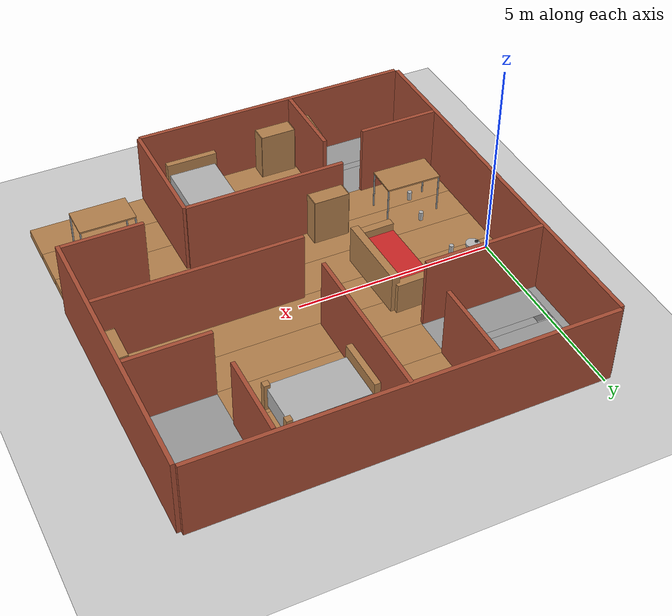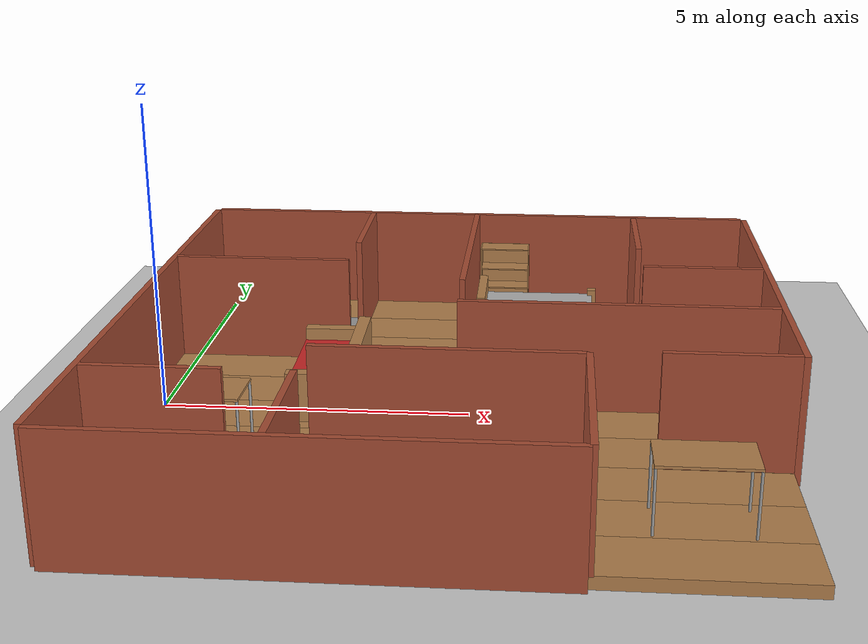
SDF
<sdf version="1.6">
 <world name="default">
  <light name="sun" type="directional">
   <pose>0 0 10 0 -0 0</pose>
   <diffuse>0.8 0.8 0.8 1</diffuse>
   <specular>0.1 0.1 0.1 1</specular>
   <attenuation>
    <range>1000</range>
    <constant>0.9</constant>
    <linear>0.01</linear>
    <quadratic>0.001</quadratic>
   </attenuation>
   <direction>-0.5 0.5 -1</direction>
  </light>
  <model name="ground_plane">
   <static>1</static>
   <link name="link">
    <collision name="collision">
     <geometry><plane><normal>0 0 1</normal><size>100 100</size></plane></geometry>
     <surface><friction><ode><mu>100</mu><mu2>50</mu2></ode></friction></surface>
    </collision>
    <visual name="visual">
     <cast_shadows>0</cast_shadows>
     <geometry><plane><normal>0 0 1</normal><size>100 100</size></plane></geometry>
     <material>
      <script><uri>file://media/materials/scripts/gazebo.material</uri><name>Gazebo/Grey</name></script>
     </material>
    </visual>
   </link>
  </model>
  <gravity>0 0 -9.8</gravity>
  <magnetic_field>6e-06 2.3e-05 -4.2e-05</magnetic_field>
  <atmosphere type="adiabatic"/>
  <physics name="default_physics" default="0" type="ode">
   <max_step_size>0.001</max_step_size>
   <real_time_factor>1</real_time_factor>
   <real_time_update_rate>1000</real_time_update_rate>
  </physics>
  <scene><ambient>0.4 0.4 0.4 1</ambient><background>0.7 0.7 0.7 1</background><shadows>1</shadows></scene>
  <spherical_coordinates>
   <surface_model>EARTH_WGS84</surface_model>
   <latitude_deg>0</latitude_deg>
   <longitude_deg>0</longitude_deg>
   <elevation>0</elevation>
   <heading_deg>0</heading_deg>
  </spherical_coordinates>
  <model name="beer">
   <link name="link">
    <pose>0 0 0.115 0 -0 0</pose>
    <inertial>
     <mass>0.39</mass>
     <inertia><ixx>0.00058</ixx><ixy>0</ixy><ixz>0</ixz><iyy>0.00058</iyy><iyz>0</iyz><izz>0.00019</izz></inertia>
    </inertial>
    <collision name="collision">
     <geometry><cylinder><radius>0.055</radius><length>0.23</length></cylinder></geometry>
    </collision>
    <visual name="visual">
     <geometry><cylinder><radius>0.055</radius><length>0.23</length></cylinder></geometry>
     <material>
      <script>
       <uri>model://beer/materials/scripts</uri>
       <uri>model://beer/materials/textures</uri>
       <name>Beer/Diffuse</name>
      </script>
     </material>
    </visual>
   </link>
   <pose>1.03601 -1.42637 0.19999 1e-06 -2.7e-05 0.001528</pose>
  </model>
  <model name="beer_clone">
   <link name="link">
    <pose>0 0 0.115 0 -0 0</pose>
    <inertial>
     <mass>0.39</mass>
     <inertia><ixx>0.00058</ixx><ixy>0</ixy><ixz>0</ixz><iyy>0.00058</iyy><iyz>0</iyz><izz>0.00019</izz></inertia>
    </inertial>
    <collision name="collision">
     <geometry><cylinder><radius>0.055</radius><length>0.23</length></cylinder></geometry>
    </collision>
    <visual name="visual">
     <geometry><cylinder><radius>0.055</radius><length>0.23</length></cylinder></geometry>
     <material>
      <script>
       <uri>model://beer/materials/scripts</uri>
       <uri>model://beer/materials/textures</uri>
       <name>Beer/Diffuse</name>
      </script>
     </material>
    </visual>
   </link>
   <pose>0.999981 0.0001 0.199992 3.1e-05 -3e-06 0.003682</pose>
  </model>
  <model name="beer_clone_0">
   <link name="link">
    <pose>0 0 0.115 0 -0 0</pose>
    <inertial>
     <mass>0.39</mass>
     <inertia><ixx>0.00058</ixx><ixy>0</ixy><ixz>0</ixz><iyy>0.00058</iyy><iyz>0</iyz><izz>0.00019</izz></inertia>
    </inertial>
    <collision name="collision">
     <geometry><cylinder><radius>0.055</radius><length>0.23</length></cylinder></geometry>
    </collision>
    <visual name="visual">
     <geometry><cylinder><radius>0.055</radius><length>0.23</length></cylinder></geometry>
     <material>
      <script>
       <uri>model://beer/materials/scripts</uri>
       <uri>model://beer/materials/textures</uri>
       <name>Beer/Diffuse</name>
      </script>
     </material>
    </visual>
   </link>
   <pose>0.906193 -2.25098 0.200001 3e-06 -2.5e-05 0.002007</pose>
  </model>
  <model name="beer_clone_1">
   <link name="link">
    <pose>0 0 0.115 0 -0 0</pose>
    <inertial>
     <mass>0.39</mass>
     <inertia><ixx>0.00058</ixx><ixy>0</ixy><ixz>0</ixz><iyy>0.00058</iyy><iyz>0</iyz><izz>0.00019</izz></inertia>
    </inertial>
    <collision name="collision">
     <geometry><cylinder><radius>0.055</radius><length>0.23</length></cylinder></geometry>
    </collision>
    <visual name="visual">
     <geometry><cylinder><radius>0.055</radius><length>0.23</length></cylinder></geometry>
     <material>
      <script>
       <uri>model://beer/materials/scripts</uri>
       <uri>model://beer/materials/textures</uri>
       <name>Beer/Diffuse</name>
      </script>
     </material>
    </visual>
   </link>
   <pose>0.858582 3.99802 0.199996 2.6e-05 0.000105 0.000698</pose>
  </model>
  <model name="beer_clone_2">
   <link name="link">
    <pose>0 0 0.115 0 -0 0</pose>
    <inertial>
     <mass>0.39</mass>
     <inertia><ixx>0.00058</ixx><ixy>0</ixy><ixz>0</ixz><iyy>0.00058</iyy><iyz>0</iyz><izz>0.00019</izz></inertia>
    </inertial>
    <collision name="collision">
     <geometry><cylinder><radius>0.055</radius><length>0.23</length></cylinder></geometry>
    </collision>
    <visual name="visual">
     <geometry><cylinder><radius>0.055</radius><length>0.23</length></cylinder></geometry>
     <material>
      <script>
       <uri>model://beer/materials/scripts</uri>
       <uri>model://beer/materials/textures</uri>
       <name>Beer/Diffuse</name>
      </script>
     </material>
    </visual>
   </link>
   <pose>1.49167 4.01205 0.200006 2.8e-05 0.000107 -5e-05</pose>
  </model>
  <model name="beer_clone_3">
   <link name="link">
    <pose>0 0 0.115 0 -0 0</pose>
    <inertial>
     <mass>0.39</mass>
     <inertia><ixx>0.00058</ixx><ixy>0</ixy><ixz>0</ixz><iyy>0.00058</iyy><iyz>0</iyz><izz>0.00019</izz></inertia>
    </inertial>
    <collision name="collision">
     <geometry><cylinder><radius>0.055</radius><length>0.23</length></cylinder></geometry>
    </collision>
    <visual name="visual">
     <geometry><cylinder><radius>0.055</radius><length>0.23</length></cylinder></geometry>
     <material>
      <script>
       <uri>model://beer/materials/scripts</uri>
       <uri>model://beer/materials/textures</uri>
       <name>Beer/Diffuse</name>
      </script>
     </material>
    </visual>
   </link>
   <pose>4.12383 -3.89543 0.19999 -1e-06 2.6e-05 0.001054</pose>
  </model>
  <model name="table_1_clone_0">
   <static>0</static>
   <link name="link">
    <collision name="surface">
     <pose>0 0 1 0 -0 0</pose>
     <geometry><box><size>1.5 0.8 0.03</size></box></geometry>
     <surface><friction><ode><mu>0.6</mu><mu2>0.6</mu2></ode></friction></surface>
    </collision>
    <visual name="visual1">
     <pose>0 0 1 0 -0 0</pose>
     <geometry><box><size>1.4 0.8 0.04</size></box></geometry>
     <material>
      <script><uri>file://media/materials/scripts/gazebo.material</uri><name>Gazebo/Wood</name></script>
     </material>
    </visual>
    <collision name="front_left_leg">
     <pose>0.68 0.38 0.5 0 -0 0</pose>
     <geometry><cylinder><radius>0.02</radius><length>1</length></cylinder></geometry>
    </collision>
    <visual name="front_left_leg">
     <pose>0.68 0.38 0.5 0 -0 0</pose>
     <geometry><cylinder><radius>0.02</radius><length>1</length></cylinder></geometry>
     <material>
      <script><uri>file://media/materials/scripts/gazebo.material</uri><name>Gazebo/Grey</name></script>
     </material>
    </visual>
    <collision name="front_right_leg">
     <pose>0.68 -0.38 0.5 0 -0 0</pose>
     <geometry><cylinder><radius>0.02</radius><length>1</length></cylinder></geometry>
    </collision>
    <visual name="front_right_leg">
     <pose>0.68 -0.38 0.5 0 -0 0</pose>
     <geometry><cylinder><radius>0.02</radius><length>1</length></cylinder></geometry>
     <material>
      <script><uri>file://media/materials/scripts/gazebo.material</uri><name>Gazebo/Grey</name></script>
     </material>
    </visual>
    <collision name="back_right_leg">
     <pose>-0.68 -0.38 0.5 0 -0 0</pose>
     <geometry><cylinder><radius>0.02</radius><length>1</length></cylinder></geometry>
    </collision>
    <visual name="back_right_leg">
     <pose>-0.68 -0.38 0.5 0 -0 0</pose>
     <geometry><cylinder><radius>0.02</radius><length>1</length></cylinder></geometry>
     <material>
      <script><uri>file://media/materials/scripts/gazebo.material</uri><name>Gazebo/Grey</name></script>
     </material>
    </visual>
    <collision name="back_left_leg">
     <pose>-0.68 0.38 0.5 0 -0 0</pose>
     <geometry><cylinder><radius>0.02</radius><length>1</length></cylinder></geometry>
    </collision>
    <visual name="back_left_leg">
     <pose>-0.68 0.38 0.5 0 -0 0</pose>
     <geometry><cylinder><radius>0.02</radius><length>1</length></cylinder></geometry>
     <material>
      <script><uri>file://media/materials/scripts/gazebo.material</uri><name>Gazebo/Grey</name></script>
     </material>
    </visual>
    <inertial>
     <inertia><ixx>1</ixx><ixy>0</ixy><ixz>0</ixz><iyy>1</iyy><iyz>0</iyz><izz>1</izz></inertia>
     <mass>1</mass>
    </inertial>
   </link>
   <pose>1.15753 -2.01599 0.19999 0 0 -0.017169</pose>
  </model>
  <model name="table_1_clone_1">
   <static>0</static>
   <link name="link">
    <collision name="surface">
     <pose>0 0 1 0 -0 0</pose>
     <geometry><box><size>1.5 0.8 0.03</size></box></geometry>
     <surface><friction><ode><mu>0.6</mu><mu2>0.6</mu2></ode></friction></surface>
    </collision>
    <visual name="visual1">
     <pose>0 0 1 0 -0 0</pose>
     <geometry><box><size>1.4 0.8 0.04</size></box></geometry>
     <material>
      <script><uri>file://media/materials/scripts/gazebo.material</uri><name>Gazebo/Wood</name></script>
     </material>
    </visual>
    <collision name="front_left_leg">
     <pose>0.68 0.38 0.5 0 -0 0</pose>
     <geometry><cylinder><radius>0.02</radius><length>1</length></cylinder></geometry>
    </collision>
    <visual name="front_left_leg">
     <pose>0.68 0.38 0.5 0 -0 0</pose>
     <geometry><cylinder><radius>0.02</radius><length>1</length></cylinder></geometry>
     <material>
      <script><uri>file://media/materials/scripts/gazebo.material</uri><name>Gazebo/Grey</name></script>
     </material>
    </visual>
    <collision name="front_right_leg">
     <pose>0.68 -0.38 0.5 0 -0 0</pose>
     <geometry><cylinder><radius>0.02</radius><length>1</length></cylinder></geometry>
    </collision>
    <visual name="front_right_leg">
     <pose>0.68 -0.38 0.5 0 -0 0</pose>
     <geometry><cylinder><radius>0.02</radius><length>1</length></cylinder></geometry>
     <material>
      <script><uri>file://media/materials/scripts/gazebo.material</uri><name>Gazebo/Grey</name></script>
     </material>
    </visual>
    <collision name="back_right_leg">
     <pose>-0.68 -0.38 0.5 0 -0 0</pose>
     <geometry><cylinder><radius>0.02</radius><length>1</length></cylinder></geometry>
    </collision>
    <visual name="back_right_leg">
     <pose>-0.68 -0.38 0.5 0 -0 0</pose>
     <geometry><cylinder><radius>0.02</radius><length>1</length></cylinder></geometry>
     <material>
      <script><uri>file://media/materials/scripts/gazebo.material</uri><name>Gazebo/Grey</name></script>
     </material>
    </visual>
    <collision name="back_left_leg">
     <pose>-0.68 0.38 0.5 0 -0 0</pose>
     <geometry><cylinder><radius>0.02</radius><length>1</length></cylinder></geometry>
    </collision>
    <visual name="back_left_leg">
     <pose>-0.68 0.38 0.5 0 -0 0</pose>
     <geometry><cylinder><radius>0.02</radius><length>1</length></cylinder></geometry>
     <material>
      <script><uri>file://media/materials/scripts/gazebo.material</uri><name>Gazebo/Grey</name></script>
     </material>
    </visual>
    <inertial>
     <inertia><ixx>1</ixx><ixy>0</ixy><ixz>0</ixz><iyy>1</iyy><iyz>0</iyz><izz>1</izz></inertia>
     <mass>1</mass>
    </inertial>
   </link>
   <pose>8.36915 -3.69644 0.199992 -1e-06 1e-06 4.6e-05</pose>
  </model>
  <model name="bookshelf">
   <static>1</static>
   <link name="link">
    <inertial><mass>1</mass></inertial>
    <collision name="back">
     <pose>0 0.005 0.6 0 -0 0</pose>
     <geometry><box><size>0.9 0.01 1.2</size></box></geometry>
    </collision>
    <visual name="visual1">
     <pose>0 0.005 0.6 0 -0 0</pose>
     <geometry><box><size>0.9 0.01 1.2</size></box></geometry>
     <material>
      <script><uri>file://media/materials/scripts/gazebo.material</uri><name>Gazebo/Wood</name></script>
     </material>
    </visual>
    <collision name="left_side">
     <pose>0.45 -0.195 0.6 0 -0 0</pose>
     <geometry><box><size>0.02 0.4 1.2</size></box></geometry>
    </collision>
    <visual name="visual2">
     <pose>0.45 -0.195 0.6 0 -0 0</pose>
     <geometry><box><size>0.02 0.4 1.2</size></box></geometry>
     <material>
      <script><uri>file://media/materials/scripts/gazebo.material</uri><name>Gazebo/Wood</name></script>
     </material>
    </visual>
    <collision name="right_side">
     <pose>-0.45 -0.195 0.6 0 -0 0</pose>
     <geometry><box><size>0.02 0.4 1.2</size></box></geometry>
    </collision>
    <visual name="visual3">
     <pose>-0.45 -0.195 0.6 0 -0 0</pose>
     <geometry><box><size>0.02 0.4 1.2</size></box></geometry>
     <material>
      <script><uri>file://media/materials/scripts/gazebo.material</uri><name>Gazebo/Wood</name></script>
     </material>
    </visual>
    <collision name="bottom">
     <pose>0 -0.195 0.03 0 -0 0</pose>
     <geometry><box><size>0.88 0.4 0.06</size></box></geometry>
    </collision>
    <visual name="visual4">
     <pose>0 -0.195 0.03 0 -0 0</pose>
     <geometry><box><size>0.88 0.4 0.06</size></box></geometry>
     <material>
      <script><uri>file://media/materials/scripts/gazebo.material</uri><name>Gazebo/Wood</name></script>
     </material>
    </visual>
    <collision name="top">
     <pose>0 -0.195 1.19 0 -0 0</pose>
     <geometry><box><size>0.88 0.4 0.02</size></box></geometry>
    </collision>
    <visual name="visual5">
     <pose>0 -0.195 1.19 0 -0 0</pose>
     <geometry><box><size>0.88 0.4 0.02</size></box></geometry>
     <material>
      <script><uri>file://media/materials/scripts/gazebo.material</uri><name>Gazebo/Wood</name></script>
     </material>
    </visual>
    <collision name="low_shelf">
     <pose>0 -0.195 0.43 0 -0 0</pose>
     <geometry><box><size>0.88 0.4 0.02</size></box></geometry>
    </collision>
    <visual name="visual6">
     <pose>0 -0.195 0.43 0 -0 0</pose>
     <geometry><box><size>0.88 0.4 0.02</size></box></geometry>
     <material>
      <script><uri>file://media/materials/scripts/gazebo.material</uri><name>Gazebo/Wood</name></script>
     </material>
    </visual>
    <collision name="high_shelf">
     <pose>0 -0.195 0.8 0 -0 0</pose>
     <geometry><box><size>0.88 0.4 0.02</size></box></geometry>
    </collision>
    <visual name="visual7">
     <pose>0 -0.195 0.8 0 -0 0</pose>
     <geometry><box><size>0.88 0.4 0.02</size></box></geometry>
     <material>
      <script><uri>file://media/materials/scripts/gazebo.material</uri><name>Gazebo/Wood</name></script>
     </material>
    </visual>
   </link>
   <pose>3.3336 -1.72318 0.202596 0 -0 0</pose>
  </model>
  <model name="bookshelf_clone">
   <static>1</static>
   <link name="link">
    <inertial><mass>1</mass></inertial>
    <collision name="back">
     <pose>0 0.005 0.6 0 -0 0</pose>
     <geometry><box><size>0.9 0.01 1.2</size></box></geometry>
    </collision>
    <visual name="visual1">
     <pose>0 0.005 0.6 0 -0 0</pose>
     <geometry><box><size>0.9 0.01 1.2</size></box></geometry>
     <material>
      <script><uri>file://media/materials/scripts/gazebo.material</uri><name>Gazebo/Wood</name></script>
     </material>
    </visual>
    <collision name="left_side">
     <pose>0.45 -0.195 0.6 0 -0 0</pose>
     <geometry><box><size>0.02 0.4 1.2</size></box></geometry>
    </collision>
    <visual name="visual2">
     <pose>0.45 -0.195 0.6 0 -0 0</pose>
     <geometry><box><size>0.02 0.4 1.2</size></box></geometry>
     <material>
      <script><uri>file://media/materials/scripts/gazebo.material</uri><name>Gazebo/Wood</name></script>
     </material>
    </visual>
    <collision name="right_side">
     <pose>-0.45 -0.195 0.6 0 -0 0</pose>
     <geometry><box><size>0.02 0.4 1.2</size></box></geometry>
    </collision>
    <visual name="visual3">
     <pose>-0.45 -0.195 0.6 0 -0 0</pose>
     <geometry><box><size>0.02 0.4 1.2</size></box></geometry>
     <material>
      <script><uri>file://media/materials/scripts/gazebo.material</uri><name>Gazebo/Wood</name></script>
     </material>
    </visual>
    <collision name="bottom">
     <pose>0 -0.195 0.03 0 -0 0</pose>
     <geometry><box><size>0.88 0.4 0.06</size></box></geometry>
    </collision>
    <visual name="visual4">
     <pose>0 -0.195 0.03 0 -0 0</pose>
     <geometry><box><size>0.88 0.4 0.06</size></box></geometry>
     <material>
      <script><uri>file://media/materials/scripts/gazebo.material</uri><name>Gazebo/Wood</name></script>
     </material>
    </visual>
    <collision name="top">
     <pose>0 -0.195 1.19 0 -0 0</pose>
     <geometry><box><size>0.88 0.4 0.02</size></box></geometry>
    </collision>
    <visual name="visual5">
     <pose>0 -0.195 1.19 0 -0 0</pose>
     <geometry><box><size>0.88 0.4 0.02</size></box></geometry>
     <material>
      <script><uri>file://media/materials/scripts/gazebo.material</uri><name>Gazebo/Wood</name></script>
     </material>
    </visual>
    <collision name="low_shelf">
     <pose>0 -0.195 0.43 0 -0 0</pose>
     <geometry><box><size>0.88 0.4 0.02</size></box></geometry>
    </collision>
    <visual name="visual6">
     <pose>0 -0.195 0.43 0 -0 0</pose>
     <geometry><box><size>0.88 0.4 0.02</size></box></geometry>
     <material>
      <script><uri>file://media/materials/scripts/gazebo.material</uri><name>Gazebo/Wood</name></script>
     </material>
    </visual>
    <collision name="high_shelf">
     <pose>0 -0.195 0.8 0 -0 0</pose>
     <geometry><box><size>0.88 0.4 0.02</size></box></geometry>
    </collision>
    <visual name="visual7">
     <pose>0 -0.195 0.8 0 -0 0</pose>
     <geometry><box><size>0.88 0.4 0.02</size></box></geometry>
     <material>
      <script><uri>file://media/materials/scripts/gazebo.material</uri><name>Gazebo/Wood</name></script>
     </material>
    </visual>
   </link>
   <pose>3.3921 -4.66436 0.202596 0 -0 0</pose>
  </model>
  <model name="bookshelf_clone_0">
   <static>1</static>
   <link name="link">
    <inertial><mass>1</mass></inertial>
    <collision name="back">
     <pose>0 0.005 0.6 0 -0 0</pose>
     <geometry><box><size>0.9 0.01 1.2</size></box></geometry>
    </collision>
    <visual name="visual1">
     <pose>0 0.005 0.6 0 -0 0</pose>
     <geometry><box><size>0.9 0.01 1.2</size></box></geometry>
     <material>
      <script><uri>file://media/materials/scripts/gazebo.material</uri><name>Gazebo/Wood</name></script>
     </material>
    </visual>
    <collision name="left_side">
     <pose>0.45 -0.195 0.6 0 -0 0</pose>
     <geometry><box><size>0.02 0.4 1.2</size></box></geometry>
    </collision>
    <visual name="visual2">
     <pose>0.45 -0.195 0.6 0 -0 0</pose>
     <geometry><box><size>0.02 0.4 1.2</size></box></geometry>
     <material>
      <script><uri>file://media/materials/scripts/gazebo.material</uri><name>Gazebo/Wood</name></script>
     </material>
    </visual>
    <collision name="right_side">
     <pose>-0.45 -0.195 0.6 0 -0 0</pose>
     <geometry><box><size>0.02 0.4 1.2</size></box></geometry>
    </collision>
    <visual name="visual3">
     <pose>-0.45 -0.195 0.6 0 -0 0</pose>
     <geometry><box><size>0.02 0.4 1.2</size></box></geometry>
     <material>
      <script><uri>file://media/materials/scripts/gazebo.material</uri><name>Gazebo/Wood</name></script>
     </material>
    </visual>
    <collision name="bottom">
     <pose>0 -0.195 0.03 0 -0 0</pose>
     <geometry><box><size>0.88 0.4 0.06</size></box></geometry>
    </collision>
    <visual name="visual4">
     <pose>0 -0.195 0.03 0 -0 0</pose>
     <geometry><box><size>0.88 0.4 0.06</size></box></geometry>
     <material>
      <script><uri>file://media/materials/scripts/gazebo.material</uri><name>Gazebo/Wood</name></script>
     </material>
    </visual>
    <collision name="top">
     <pose>0 -0.195 1.19 0 -0 0</pose>
     <geometry><box><size>0.88 0.4 0.02</size></box></geometry>
    </collision>
    <visual name="visual5">
     <pose>0 -0.195 1.19 0 -0 0</pose>
     <geometry><box><size>0.88 0.4 0.02</size></box></geometry>
     <material>
      <script><uri>file://media/materials/scripts/gazebo.material</uri><name>Gazebo/Wood</name></script>
     </material>
    </visual>
    <collision name="low_shelf">
     <pose>0 -0.195 0.43 0 -0 0</pose>
     <geometry><box><size>0.88 0.4 0.02</size></box></geometry>
    </collision>
    <visual name="visual6">
     <pose>0 -0.195 0.43 0 -0 0</pose>
     <geometry><box><size>0.88 0.4 0.02</size></box></geometry>
     <material>
      <script><uri>file://media/materials/scripts/gazebo.material</uri><name>Gazebo/Wood</name></script>
     </material>
    </visual>
    <collision name="high_shelf">
     <pose>0 -0.195 0.8 0 -0 0</pose>
     <geometry><box><size>0.88 0.4 0.02</size></box></geometry>
    </collision>
    <visual name="visual7">
     <pose>0 -0.195 0.8 0 -0 0</pose>
     <geometry><box><size>0.88 0.4 0.02</size></box></geometry>
     <material>
      <script><uri>file://media/materials/scripts/gazebo.material</uri><name>Gazebo/Wood</name></script>
     </material>
    </visual>
   </link>
   <pose>2.39209 -4.6394 0.202596 0 -0 1.52697</pose>
  </model>
  <model name="bookshelf_clone_1">
   <static>1</static>
   <link name="link">
    <inertial><mass>1</mass></inertial>
    <collision name="back">
     <pose>0 0.005 0.6 0 -0 0</pose>
     <geometry><box><size>0.9 0.01 1.2</size></box></geometry>
    </collision>
    <visual name="visual1">
     <pose>0 0.005 0.6 0 -0 0</pose>
     <geometry><box><size>0.9 0.01 1.2</size></box></geometry>
     <material>
      <script><uri>file://media/materials/scripts/gazebo.material</uri><name>Gazebo/Wood</name></script>
     </material>
    </visual>
    <collision name="left_side">
     <pose>0.45 -0.195 0.6 0 -0 0</pose>
     <geometry><box><size>0.02 0.4 1.2</size></box></geometry>
    </collision>
    <visual name="visual2">
     <pose>0.45 -0.195 0.6 0 -0 0</pose>
     <geometry><box><size>0.02 0.4 1.2</size></box></geometry>
     <material>
      <script><uri>file://media/materials/scripts/gazebo.material</uri><name>Gazebo/Wood</name></script>
     </material>
    </visual>
    <collision name="right_side">
     <pose>-0.45 -0.195 0.6 0 -0 0</pose>
     <geometry><box><size>0.02 0.4 1.2</size></box></geometry>
    </collision>
    <visual name="visual3">
     <pose>-0.45 -0.195 0.6 0 -0 0</pose>
     <geometry><box><size>0.02 0.4 1.2</size></box></geometry>
     <material>
      <script><uri>file://media/materials/scripts/gazebo.material</uri><name>Gazebo/Wood</name></script>
     </material>
    </visual>
    <collision name="bottom">
     <pose>0 -0.195 0.03 0 -0 0</pose>
     <geometry><box><size>0.88 0.4 0.06</size></box></geometry>
    </collision>
    <visual name="visual4">
     <pose>0 -0.195 0.03 0 -0 0</pose>
     <geometry><box><size>0.88 0.4 0.06</size></box></geometry>
     <material>
      <script><uri>file://media/materials/scripts/gazebo.material</uri><name>Gazebo/Wood</name></script>
     </material>
    </visual>
    <collision name="top">
     <pose>0 -0.195 1.19 0 -0 0</pose>
     <geometry><box><size>0.88 0.4 0.02</size></box></geometry>
    </collision>
    <visual name="visual5">
     <pose>0 -0.195 1.19 0 -0 0</pose>
     <geometry><box><size>0.88 0.4 0.02</size></box></geometry>
     <material>
      <script><uri>file://media/materials/scripts/gazebo.material</uri><name>Gazebo/Wood</name></script>
     </material>
    </visual>
    <collision name="low_shelf">
     <pose>0 -0.195 0.43 0 -0 0</pose>
     <geometry><box><size>0.88 0.4 0.02</size></box></geometry>
    </collision>
    <visual name="visual6">
     <pose>0 -0.195 0.43 0 -0 0</pose>
     <geometry><box><size>0.88 0.4 0.02</size></box></geometry>
     <material>
      <script><uri>file://media/materials/scripts/gazebo.material</uri><name>Gazebo/Wood</name></script>
     </material>
    </visual>
    <collision name="high_shelf">
     <pose>0 -0.195 0.8 0 -0 0</pose>
     <geometry><box><size>0.88 0.4 0.02</size></box></geometry>
    </collision>
    <visual name="visual7">
     <pose>0 -0.195 0.8 0 -0 0</pose>
     <geometry><box><size>0.88 0.4 0.02</size></box></geometry>
     <material>
      <script><uri>file://media/materials/scripts/gazebo.material</uri><name>Gazebo/Wood</name></script>
     </material>
    </visual>
   </link>
   <pose>5.38847 4.85222 0.241845 0 -0 0</pose>
  </model>
  <model name="bad_1">
   <link name="link_0">
    <pose>-0.25 0 0.35 0 -0 0</pose>
    <inertial>
     <mass>1</mass>
     <inertia>
      <ixx>0.166667</ixx>
      <ixy>0</ixy>
      <ixz>0</ixz>
      <iyy>0.166667</iyy>
      <iyz>0</iyz>
      <izz>0.166667</izz>
     </inertia>
    </inertial>
    <visual name="visual">
     <geometry><box><size>2 1.2 0.5</size></box></geometry>
     <material>
      <lighting>1</lighting>
      <script><uri>file://media/materials/scripts/gazebo.material</uri><name>Gazebo/PioneerBody</name></script>
      <ambient>0.3 0.3 0.3 1</ambient>
      <diffuse>0.7 0.7 0.7 1</diffuse>
      <specular>0.01 0.01 0.01 1</specular>
      <emissive>0 0 0 1</emissive>
      <shader type="vertex"><normal_map>__default__</normal_map></shader>
     </material>
    </visual>
    <collision name="collision">
     <geometry><box><size>2 1.2 0.5</size></box></geometry>
     <surface>
      <friction>
       <ode><mu>1</mu><mu2>1</mu2><fdir1>0 0 0</fdir1><slip1>0</slip1><slip2>0</slip2></ode>
       <torsional>
        <coefficient>1</coefficient>
        <patch_radius>0</patch_radius>
        <surface_radius>0</surface_radius>
        <use_patch_radius>1</use_patch_radius>
        <ode><slip>0</slip></ode>
       </torsional>
      </friction>
      <bounce><restitution_coefficient>0</restitution_coefficient><threshold>1e+06</threshold></bounce>
      <contact>
       <collide_without_contact>0</collide_without_contact>
       <collide_without_contact_bitmask>1</collide_without_contact_bitmask>
       <collide_bitmask>1</collide_bitmask>
       <ode>
        <soft_cfm>0</soft_cfm>
        <soft_erp>0.2</soft_erp>
        <kp>1e+13</kp>
        <kd>1</kd>
        <max_vel>0.01</max_vel>
        <min_depth>0</min_depth>
       </ode>
       <bullet>
        <split_impulse>1</split_impulse>
        <split_impulse_penetration_threshold>-0.01</split_impulse_penetration_threshold>
        <soft_cfm>0</soft_cfm>
        <soft_erp>0.2</soft_erp>
        <kp>1e+13</kp>
        <kd>1</kd>
       </bullet>
      </contact>
     </surface>
    </collision>
   </link>
   <link name="link_1">
    <pose>-1.25 0 0.45 0 -0 0</pose>
    <inertial>
     <mass>1</mass>
     <inertia>
      <ixx>0.166667</ixx>
      <ixy>0</ixy>
      <ixz>0</ixz>
      <iyy>0.166667</iyy>
      <iyz>0</iyz>
      <izz>0.166667</izz>
     </inertia>
    </inertial>
    <visual name="visual">
     <geometry><box><size>0.15 1.3 0.9</size></box></geometry>
     <material>
      <lighting>1</lighting>
      <script><uri>file://media/materials/scripts/gazebo.material</uri><name>Gazebo/Wood</name></script>
      <ambient>0.3 0.3 0.3 1</ambient>
      <diffuse>0.7 0.7 0.7 1</diffuse>
      <specular>0.01 0.01 0.01 1</specular>
      <emissive>0 0 0 1</emissive>
      <shader type="vertex"><normal_map>__default__</normal_map></shader>
     </material>
    </visual>
    <collision name="collision">
     <geometry><box><size>0.15 1.3 0.9</size></box></geometry>
     <surface>
      <friction>
       <ode><mu>1</mu><mu2>1</mu2><fdir1>0 0 0</fdir1><slip1>0</slip1><slip2>0</slip2></ode>
       <torsional>
        <coefficient>1</coefficient>
        <patch_radius>0</patch_radius>
        <surface_radius>0</surface_radius>
        <use_patch_radius>1</use_patch_radius>
        <ode><slip>0</slip></ode>
       </torsional>
      </friction>
      <bounce><restitution_coefficient>0</restitution_coefficient><threshold>1e+06</threshold></bounce>
      <contact>
       <collide_without_contact>0</collide_without_contact>
       <collide_without_contact_bitmask>1</collide_without_contact_bitmask>
       <collide_bitmask>1</collide_bitmask>
       <ode>
        <soft_cfm>0</soft_cfm>
        <soft_erp>0.2</soft_erp>
        <kp>1e+13</kp>
        <kd>1</kd>
        <max_vel>0.01</max_vel>
        <min_depth>0</min_depth>
       </ode>
       <bullet>
        <split_impulse>1</split_impulse>
        <split_impulse_penetration_threshold>-0.01</split_impulse_penetration_threshold>
        <soft_cfm>0</soft_cfm>
        <soft_erp>0.2</soft_erp>
        <kp>1e+13</kp>
        <kd>1</kd>
       </bullet>
      </contact>
     </surface>
    </collision>
   </link>
   <link name="link_1_clone">
    <pose>0.75 -0.55 0.35 0 -0 0</pose>
    <inertial>
     <mass>1</mass>
     <inertia>
      <ixx>0.166667</ixx>
      <ixy>0</ixy>
      <ixz>0</ixz>
      <iyy>0.166667</iyy>
      <iyz>0</iyz>
      <izz>0.166667</izz>
     </inertia>
    </inertial>
    <visual name="visual">
     <geometry><box><size>0.15 0.15 0.7</size></box></geometry>
     <material>
      <lighting>1</lighting>
      <script><uri>file://media/materials/scripts/gazebo.material</uri><name>Gazebo/Wood</name></script>
      <ambient>0.3 0.3 0.3 1</ambient>
      <diffuse>0.7 0.7 0.7 1</diffuse>
      <specular>0.01 0.01 0.01 1</specular>
      <emissive>0 0 0 1</emissive>
      <shader type="vertex"><normal_map>__default__</normal_map></shader>
     </material>
    </visual>
    <collision name="collision">
     <geometry><box><size>0.15 0.15 0.7</size></box></geometry>
     <surface>
      <friction>
       <ode><mu>1</mu><mu2>1</mu2><fdir1>0 0 0</fdir1><slip1>0</slip1><slip2>0</slip2></ode>
       <torsional>
        <coefficient>1</coefficient>
        <patch_radius>0</patch_radius>
        <surface_radius>0</surface_radius>
        <use_patch_radius>1</use_patch_radius>
        <ode><slip>0</slip></ode>
       </torsional>
      </friction>
      <bounce><restitution_coefficient>0</restitution_coefficient><threshold>1e+06</threshold></bounce>
      <contact>
       <collide_without_contact>0</collide_without_contact>
       <collide_without_contact_bitmask>1</collide_without_contact_bitmask>
       <collide_bitmask>1</collide_bitmask>
       <ode>
        <soft_cfm>0</soft_cfm>
        <soft_erp>0.2</soft_erp>
        <kp>1e+13</kp>
        <kd>1</kd>
        <max_vel>0.01</max_vel>
        <min_depth>0</min_depth>
       </ode>
       <bullet>
        <split_impulse>1</split_impulse>
        <split_impulse_penetration_threshold>-0.01</split_impulse_penetration_threshold>
        <soft_cfm>0</soft_cfm>
        <soft_erp>0.2</soft_erp>
        <kp>1e+13</kp>
        <kd>1</kd>
       </bullet>
      </contact>
     </surface>
    </collision>
   </link>
   <link name="link_1_clone_clone">
    <pose>0.75 0.55 0.35 0 -0 0</pose>
    <inertial>
     <mass>1</mass>
     <inertia>
      <ixx>0.166667</ixx>
      <ixy>0</ixy>
      <ixz>0</ixz>
      <iyy>0.166667</iyy>
      <iyz>0</iyz>
      <izz>0.166667</izz>
     </inertia>
    </inertial>
    <visual name="visual">
     <geometry><box><size>0.15 0.15 0.7</size></box></geometry>
     <material>
      <lighting>1</lighting>
      <script><uri>file://media/materials/scripts/gazebo.material</uri><name>Gazebo/Wood</name></script>
      <ambient>0.3 0.3 0.3 1</ambient>
      <diffuse>0.7 0.7 0.7 1</diffuse>
      <specular>0.01 0.01 0.01 1</specular>
      <emissive>0 0 0 1</emissive>
      <shader type="vertex"><normal_map>__default__</normal_map></shader>
     </material>
    </visual>
    <collision name="collision">
     <geometry><box><size>0.15 0.15 0.7</size></box></geometry>
     <surface>
      <friction>
       <ode><mu>1</mu><mu2>1</mu2><fdir1>0 0 0</fdir1><slip1>0</slip1><slip2>0</slip2></ode>
       <torsional>
        <coefficient>1</coefficient>
        <patch_radius>0</patch_radius>
        <surface_radius>0</surface_radius>
        <use_patch_radius>1</use_patch_radius>
        <ode><slip>0</slip></ode>
       </torsional>
      </friction>
      <bounce><restitution_coefficient>0</restitution_coefficient><threshold>1e+06</threshold></bounce>
      <contact>
       <collide_without_contact>0</collide_without_contact>
       <collide_without_contact_bitmask>1</collide_without_contact_bitmask>
       <collide_bitmask>1</collide_bitmask>
       <ode>
        <soft_cfm>0</soft_cfm>
        <soft_erp>0.2</soft_erp>
        <kp>1e+13</kp>
        <kd>1</kd>
        <max_vel>0.01</max_vel>
        <min_depth>0</min_depth>
       </ode>
       <bullet>
        <split_impulse>1</split_impulse>
        <split_impulse_penetration_threshold>-0.01</split_impulse_penetration_threshold>
        <soft_cfm>0</soft_cfm>
        <soft_erp>0.2</soft_erp>
        <kp>1e+13</kp>
        <kd>1</kd>
       </bullet>
      </contact>
     </surface>
    </collision>
   </link>
   <joint name="link_0_JOINT_0" type="fixed">
    <parent>link_0</parent>
    <child>link_1</child>
    <physics>
     <ode><limit><cfm>0</cfm><erp>0.2</erp></limit><suspension><cfm>0</cfm><erp>0.2</erp></suspension></ode>
    </physics>
   </joint>
   <joint name="link_0_JOINT_1" type="fixed">
    <parent>link_0</parent>
    <child>link_1_clone</child>
    <physics>
     <ode><limit><cfm>0</cfm><erp>0.2</erp></limit><suspension><cfm>0</cfm><erp>0.2</erp></suspension></ode>
    </physics>
   </joint>
   <joint name="link_0_JOINT_2" type="fixed">
    <parent>link_0</parent>
    <child>link_1_clone_clone</child>
    <physics>
     <ode><limit><cfm>0</cfm><erp>0.2</erp></limit><suspension><cfm>0</cfm><erp>0.2</erp></suspension></ode>
    </physics>
   </joint>
   <static>0</static>
   <pose>6.28812 3.2494 0.2 0 -0 0.008585</pose>
  </model>
  <model name="bad_1_clone">
   <link name="link_0">
    <pose>-0.25 0 0.35 0 -0 0</pose>
    <inertial>
     <mass>1</mass>
     <inertia>
      <ixx>0.166667</ixx>
      <ixy>0</ixy>
      <ixz>0</ixz>
      <iyy>0.166667</iyy>
      <iyz>0</iyz>
      <izz>0.166667</izz>
     </inertia>
    </inertial>
    <visual name="visual">
     <geometry><box><size>2 1.2 0.5</size></box></geometry>
     <material>
      <lighting>1</lighting>
      <script><uri>file://media/materials/scripts/gazebo.material</uri><name>Gazebo/PioneerBody</name></script>
      <ambient>0.3 0.3 0.3 1</ambient>
      <diffuse>0.7 0.7 0.7 1</diffuse>
      <specular>0.01 0.01 0.01 1</specular>
      <emissive>0 0 0 1</emissive>
      <shader type="vertex"><normal_map>__default__</normal_map></shader>
     </material>
    </visual>
    <collision name="collision">
     <geometry><box><size>2 1.2 0.5</size></box></geometry>
     <surface>
      <friction>
       <ode><mu>1</mu><mu2>1</mu2><fdir1>0 0 0</fdir1><slip1>0</slip1><slip2>0</slip2></ode>
       <torsional>
        <coefficient>1</coefficient>
        <patch_radius>0</patch_radius>
        <surface_radius>0</surface_radius>
        <use_patch_radius>1</use_patch_radius>
        <ode><slip>0</slip></ode>
       </torsional>
      </friction>
      <bounce><restitution_coefficient>0</restitution_coefficient><threshold>1e+06</threshold></bounce>
      <contact>
       <collide_without_contact>0</collide_without_contact>
       <collide_without_contact_bitmask>1</collide_without_contact_bitmask>
       <collide_bitmask>1</collide_bitmask>
       <ode>
        <soft_cfm>0</soft_cfm>
        <soft_erp>0.2</soft_erp>
        <kp>1e+13</kp>
        <kd>1</kd>
        <max_vel>0.01</max_vel>
        <min_depth>0</min_depth>
       </ode>
       <bullet>
        <split_impulse>1</split_impulse>
        <split_impulse_penetration_threshold>-0.01</split_impulse_penetration_threshold>
        <soft_cfm>0</soft_cfm>
        <soft_erp>0.2</soft_erp>
        <kp>1e+13</kp>
        <kd>1</kd>
       </bullet>
      </contact>
     </surface>
    </collision>
   </link>
   <link name="link_1">
    <pose>-1.25 0 0.45 0 -0 0</pose>
    <inertial>
     <mass>1</mass>
     <inertia>
      <ixx>0.166667</ixx>
      <ixy>0</ixy>
      <ixz>0</ixz>
      <iyy>0.166667</iyy>
      <iyz>0</iyz>
      <izz>0.166667</izz>
     </inertia>
    </inertial>
    <visual name="visual">
     <geometry><box><size>0.15 1.3 0.9</size></box></geometry>
     <material>
      <lighting>1</lighting>
      <script><uri>file://media/materials/scripts/gazebo.material</uri><name>Gazebo/Wood</name></script>
      <ambient>0.3 0.3 0.3 1</ambient>
      <diffuse>0.7 0.7 0.7 1</diffuse>
      <specular>0.01 0.01 0.01 1</specular>
      <emissive>0 0 0 1</emissive>
      <shader type="vertex"><normal_map>__default__</normal_map></shader>
     </material>
    </visual>
    <collision name="collision">
     <geometry><box><size>0.15 1.3 0.9</size></box></geometry>
     <surface>
      <friction>
       <ode><mu>1</mu><mu2>1</mu2><fdir1>0 0 0</fdir1><slip1>0</slip1><slip2>0</slip2></ode>
       <torsional>
        <coefficient>1</coefficient>
        <patch_radius>0</patch_radius>
        <surface_radius>0</surface_radius>
        <use_patch_radius>1</use_patch_radius>
        <ode><slip>0</slip></ode>
       </torsional>
      </friction>
      <bounce><restitution_coefficient>0</restitution_coefficient><threshold>1e+06</threshold></bounce>
      <contact>
       <collide_without_contact>0</collide_without_contact>
       <collide_without_contact_bitmask>1</collide_without_contact_bitmask>
       <collide_bitmask>1</collide_bitmask>
       <ode>
        <soft_cfm>0</soft_cfm>
        <soft_erp>0.2</soft_erp>
        <kp>1e+13</kp>
        <kd>1</kd>
        <max_vel>0.01</max_vel>
        <min_depth>0</min_depth>
       </ode>
       <bullet>
        <split_impulse>1</split_impulse>
        <split_impulse_penetration_threshold>-0.01</split_impulse_penetration_threshold>
        <soft_cfm>0</soft_cfm>
        <soft_erp>0.2</soft_erp>
        <kp>1e+13</kp>
        <kd>1</kd>
       </bullet>
      </contact>
     </surface>
    </collision>
   </link>
   <link name="link_1_clone">
    <pose>0.75 -0.55 0.35 0 -0 0</pose>
    <inertial>
     <mass>1</mass>
     <inertia>
      <ixx>0.166667</ixx>
      <ixy>0</ixy>
      <ixz>0</ixz>
      <iyy>0.166667</iyy>
      <iyz>0</iyz>
      <izz>0.166667</izz>
     </inertia>
    </inertial>
    <visual name="visual">
     <geometry><box><size>0.15 0.15 0.7</size></box></geometry>
     <material>
      <lighting>1</lighting>
      <script><uri>file://media/materials/scripts/gazebo.material</uri><name>Gazebo/Wood</name></script>
      <ambient>0.3 0.3 0.3 1</ambient>
      <diffuse>0.7 0.7 0.7 1</diffuse>
      <specular>0.01 0.01 0.01 1</specular>
      <emissive>0 0 0 1</emissive>
      <shader type="vertex"><normal_map>__default__</normal_map></shader>
     </material>
    </visual>
    <collision name="collision">
     <geometry><box><size>0.15 0.15 0.7</size></box></geometry>
     <surface>
      <friction>
       <ode><mu>1</mu><mu2>1</mu2><fdir1>0 0 0</fdir1><slip1>0</slip1><slip2>0</slip2></ode>
       <torsional>
        <coefficient>1</coefficient>
        <patch_radius>0</patch_radius>
        <surface_radius>0</surface_radius>
        <use_patch_radius>1</use_patch_radius>
        <ode><slip>0</slip></ode>
       </torsional>
      </friction>
      <bounce><restitution_coefficient>0</restitution_coefficient><threshold>1e+06</threshold></bounce>
      <contact>
       <collide_without_contact>0</collide_without_contact>
       <collide_without_contact_bitmask>1</collide_without_contact_bitmask>
       <collide_bitmask>1</collide_bitmask>
       <ode>
        <soft_cfm>0</soft_cfm>
        <soft_erp>0.2</soft_erp>
        <kp>1e+13</kp>
        <kd>1</kd>
        <max_vel>0.01</max_vel>
        <min_depth>0</min_depth>
       </ode>
       <bullet>
        <split_impulse>1</split_impulse>
        <split_impulse_penetration_threshold>-0.01</split_impulse_penetration_threshold>
        <soft_cfm>0</soft_cfm>
        <soft_erp>0.2</soft_erp>
        <kp>1e+13</kp>
        <kd>1</kd>
       </bullet>
      </contact>
     </surface>
    </collision>
   </link>
   <link name="link_1_clone_clone">
    <pose>0.75 0.55 0.35 0 -0 0</pose>
    <inertial>
     <mass>1</mass>
     <inertia>
      <ixx>0.166667</ixx>
      <ixy>0</ixy>
      <ixz>0</ixz>
      <iyy>0.166667</iyy>
      <iyz>0</iyz>
      <izz>0.166667</izz>
     </inertia>
    </inertial>
    <visual name="visual">
     <geometry><box><size>0.15 0.15 0.7</size></box></geometry>
     <material>
      <lighting>1</lighting>
      <script><uri>file://media/materials/scripts/gazebo.material</uri><name>Gazebo/Wood</name></script>
      <ambient>0.3 0.3 0.3 1</ambient>
      <diffuse>0.7 0.7 0.7 1</diffuse>
      <specular>0.01 0.01 0.01 1</specular>
      <emissive>0 0 0 1</emissive>
      <shader type="vertex"><normal_map>__default__</normal_map></shader>
     </material>
    </visual>
    <collision name="collision">
     <geometry><box><size>0.15 0.15 0.7</size></box></geometry>
     <surface>
      <friction>
       <ode><mu>1</mu><mu2>1</mu2><fdir1>0 0 0</fdir1><slip1>0</slip1><slip2>0</slip2></ode>
       <torsional>
        <coefficient>1</coefficient>
        <patch_radius>0</patch_radius>
        <surface_radius>0</surface_radius>
        <use_patch_radius>1</use_patch_radius>
        <ode><slip>0</slip></ode>
       </torsional>
      </friction>
      <bounce><restitution_coefficient>0</restitution_coefficient><threshold>1e+06</threshold></bounce>
      <contact>
       <collide_without_contact>0</collide_without_contact>
       <collide_without_contact_bitmask>1</collide_without_contact_bitmask>
       <collide_bitmask>1</collide_bitmask>
       <ode>
        <soft_cfm>0</soft_cfm>
        <soft_erp>0.2</soft_erp>
        <kp>1e+13</kp>
        <kd>1</kd>
        <max_vel>0.01</max_vel>
        <min_depth>0</min_depth>
       </ode>
       <bullet>
        <split_impulse>1</split_impulse>
        <split_impulse_penetration_threshold>-0.01</split_impulse_penetration_threshold>
        <soft_cfm>0</soft_cfm>
        <soft_erp>0.2</soft_erp>
        <kp>1e+13</kp>
        <kd>1</kd>
       </bullet>
      </contact>
     </surface>
    </collision>
   </link>
   <joint name="link_0_JOINT_0" type="fixed">
    <parent>link_0</parent>
    <child>link_1</child>
    <physics>
     <ode><limit><cfm>0</cfm><erp>0.2</erp></limit><suspension><cfm>0</cfm><erp>0.2</erp></suspension></ode>
    </physics>
   </joint>
   <joint name="link_0_JOINT_1" type="fixed">
    <parent>link_0</parent>
    <child>link_1_clone</child>
    <physics>
     <ode><limit><cfm>0</cfm><erp>0.2</erp></limit><suspension><cfm>0</cfm><erp>0.2</erp></suspension></ode>
    </physics>
   </joint>
   <joint name="link_0_JOINT_2" type="fixed">
    <parent>link_0</parent>
    <child>link_1_clone_clone</child>
    <physics>
     <ode><limit><cfm>0</cfm><erp>0.2</erp></limit><suspension><cfm>0</cfm><erp>0.2</erp></suspension></ode>
    </physics>
   </joint>
   <static>0</static>
   <pose>5.61074 -3.79149 0.2 1e-06 -0 1.56717</pose>
  </model>
  <model name="safa">
   <link name="link_0">
    <pose>0.125 0 -0.0625 0 -0 0</pose>
    <inertial>
     <mass>1</mass>
     <inertia>
      <ixx>0.166667</ixx>
      <ixy>0</ixy>
      <ixz>0</ixz>
      <iyy>0.166667</iyy>
      <iyz>0</iyz>
      <izz>0.166667</izz>
     </inertia>
    </inertial>
    <visual name="visual">
     <geometry><box><size>1 2 0.5</size></box></geometry>
     <material>
      <lighting>1</lighting>
      <script><uri>file://media/materials/scripts/gazebo.material</uri><name>Gazebo/Red</name></script>
      <ambient>0.7 0 0 1</ambient>
      <diffuse>0.7 0 0 1</diffuse>
      <specular>0.7 0 0 1</specular>
      <emissive>0 0 0 1</emissive>
      <shader type="vertex"><normal_map>__default__</normal_map></shader>
     </material>
    </visual>
    <collision name="collision">
     <geometry><box><size>1 2 0.5</size></box></geometry>
     <surface>
      <friction>
       <ode><mu>1</mu><mu2>1</mu2><fdir1>0 0 0</fdir1><slip1>0</slip1><slip2>0</slip2></ode>
       <torsional>
        <coefficient>1</coefficient>
        <patch_radius>0</patch_radius>
        <surface_radius>0</surface_radius>
        <use_patch_radius>1</use_patch_radius>
        <ode><slip>0</slip></ode>
       </torsional>
      </friction>
      <bounce><restitution_coefficient>0</restitution_coefficient><threshold>1e+06</threshold></bounce>
      <contact>
       <collide_without_contact>0</collide_without_contact>
       <collide_without_contact_bitmask>1</collide_without_contact_bitmask>
       <collide_bitmask>1</collide_bitmask>
       <ode>
        <soft_cfm>0</soft_cfm>
        <soft_erp>0.2</soft_erp>
        <kp>1e+13</kp>
        <kd>1</kd>
        <max_vel>0.01</max_vel>
        <min_depth>0</min_depth>
       </ode>
       <bullet>
        <split_impulse>1</split_impulse>
        <split_impulse_penetration_threshold>-0.01</split_impulse_penetration_threshold>
        <soft_cfm>0</soft_cfm>
        <soft_erp>0.2</soft_erp>
        <kp>1e+13</kp>
        <kd>1</kd>
       </bullet>
      </contact>
     </surface>
    </collision>
   </link>
   <link name="link_1">
    <pose>0.125 -1 -0.0125 0 -0 0</pose>
    <inertial>
     <mass>1</mass>
     <inertia>
      <ixx>0.166667</ixx>
      <ixy>0</ixy>
      <ixz>0</ixz>
      <iyy>0.166667</iyy>
      <iyz>0</iyz>
      <izz>0.166667</izz>
     </inertia>
    </inertial>
    <visual name="visual">
     <geometry><box><size>1 0.2 0.8</size></box></geometry>
     <material>
      <lighting>1</lighting>
      <script><uri>file://media/materials/scripts/gazebo.material</uri><name>Gazebo/Wood</name></script>
      <ambient>0.3 0.3 0.3 1</ambient>
      <diffuse>0.7 0.7 0.7 1</diffuse>
      <specular>0.01 0.01 0.01 1</specular>
      <emissive>0 0 0 1</emissive>
      <shader type="vertex"><normal_map>__default__</normal_map></shader>
     </material>
    </visual>
    <collision name="collision">
     <geometry><box><size>1 0.2 0.8</size></box></geometry>
     <surface>
      <friction>
       <ode><mu>1</mu><mu2>1</mu2><fdir1>0 0 0</fdir1><slip1>0</slip1><slip2>0</slip2></ode>
       <torsional>
        <coefficient>1</coefficient>
        <patch_radius>0</patch_radius>
        <surface_radius>0</surface_radius>
        <use_patch_radius>1</use_patch_radius>
        <ode><slip>0</slip></ode>
       </torsional>
      </friction>
      <bounce><restitution_coefficient>0</restitution_coefficient><threshold>1e+06</threshold></bounce>
      <contact>
       <collide_without_contact>0</collide_without_contact>
       <collide_without_contact_bitmask>1</collide_without_contact_bitmask>
       <collide_bitmask>1</collide_bitmask>
       <ode>
        <soft_cfm>0</soft_cfm>
        <soft_erp>0.2</soft_erp>
        <kp>1e+13</kp>
        <kd>1</kd>
        <max_vel>0.01</max_vel>
        <min_depth>0</min_depth>
       </ode>
       <bullet>
        <split_impulse>1</split_impulse>
        <split_impulse_penetration_threshold>-0.01</split_impulse_penetration_threshold>
        <soft_cfm>0</soft_cfm>
        <soft_erp>0.2</soft_erp>
        <kp>1e+13</kp>
        <kd>1</kd>
       </bullet>
      </contact>
     </surface>
    </collision>
   </link>
   <link name="link_1_clone">
    <pose>0.125 1 -0.0125 0 -0 0</pose>
    <inertial>
     <mass>1</mass>
     <inertia>
      <ixx>0.166667</ixx>
      <ixy>0</ixy>
      <ixz>0</ixz>
      <iyy>0.166667</iyy>
      <iyz>0</iyz>
      <izz>0.166667</izz>
     </inertia>
    </inertial>
    <visual name="visual">
     <geometry><box><size>1 0.2 0.8</size></box></geometry>
     <material>
      <lighting>1</lighting>
      <script><uri>file://media/materials/scripts/gazebo.material</uri><name>Gazebo/Wood</name></script>
      <ambient>0.3 0.3 0.3 1</ambient>
      <diffuse>0.7 0.7 0.7 1</diffuse>
      <specular>0.01 0.01 0.01 1</specular>
      <emissive>0 0 0 1</emissive>
      <shader type="vertex"><normal_map>__default__</normal_map></shader>
     </material>
    </visual>
    <collision name="collision">
     <geometry><box><size>1 0.2 0.8</size></box></geometry>
     <surface>
      <friction>
       <ode><mu>1</mu><mu2>1</mu2><fdir1>0 0 0</fdir1><slip1>0</slip1><slip2>0</slip2></ode>
       <torsional>
        <coefficient>1</coefficient>
        <patch_radius>0</patch_radius>
        <surface_radius>0</surface_radius>
        <use_patch_radius>1</use_patch_radius>
        <ode><slip>0</slip></ode>
       </torsional>
      </friction>
      <bounce><restitution_coefficient>0</restitution_coefficient><threshold>1e+06</threshold></bounce>
      <contact>
       <collide_without_contact>0</collide_without_contact>
       <collide_without_contact_bitmask>1</collide_without_contact_bitmask>
       <collide_bitmask>1</collide_bitmask>
       <ode>
        <soft_cfm>0</soft_cfm>
        <soft_erp>0.2</soft_erp>
        <kp>1e+13</kp>
        <kd>1</kd>
        <max_vel>0.01</max_vel>
        <min_depth>0</min_depth>
       </ode>
       <bullet>
        <split_impulse>1</split_impulse>
        <split_impulse_penetration_threshold>-0.01</split_impulse_penetration_threshold>
        <soft_cfm>0</soft_cfm>
        <soft_erp>0.2</soft_erp>
        <kp>1e+13</kp>
        <kd>1</kd>
       </bullet>
      </contact>
     </surface>
    </collision>
   </link>
   <link name="link_1_clone_0">
    <pose>-0.375 0 0.0875 0 -0 0</pose>
    <inertial>
     <mass>1</mass>
     <inertia>
      <ixx>0.166667</ixx>
      <ixy>0</ixy>
      <ixz>0</ixz>
      <iyy>0.166667</iyy>
      <iyz>0</iyz>
      <izz>0.166667</izz>
     </inertia>
    </inertial>
    <visual name="visual">
     <geometry><box><size>0.2 2 1</size></box></geometry>
     <material>
      <lighting>1</lighting>
      <script><uri>file://media/materials/scripts/gazebo.material</uri><name>Gazebo/Wood</name></script>
      <ambient>0.3 0.3 0.3 1</ambient>
      <diffuse>0.7 0.7 0.7 1</diffuse>
      <specular>0.01 0.01 0.01 1</specular>
      <emissive>0 0 0 1</emissive>
      <shader type="vertex"><normal_map>__default__</normal_map></shader>
     </material>
    </visual>
    <collision name="collision">
     <geometry><box><size>0.2 2 1</size></box></geometry>
     <surface>
      <friction>
       <ode><mu>1</mu><mu2>1</mu2><fdir1>0 0 0</fdir1><slip1>0</slip1><slip2>0</slip2></ode>
       <torsional>
        <coefficient>1</coefficient>
        <patch_radius>0</patch_radius>
        <surface_radius>0</surface_radius>
        <use_patch_radius>1</use_patch_radius>
        <ode><slip>0</slip></ode>
       </torsional>
      </friction>
      <bounce><restitution_coefficient>0</restitution_coefficient><threshold>1e+06</threshold></bounce>
      <contact>
       <collide_without_contact>0</collide_without_contact>
       <collide_without_contact_bitmask>1</collide_without_contact_bitmask>
       <collide_bitmask>1</collide_bitmask>
       <ode>
        <soft_cfm>0</soft_cfm>
        <soft_erp>0.2</soft_erp>
        <kp>1e+13</kp>
        <kd>1</kd>
        <max_vel>0.01</max_vel>
        <min_depth>0</min_depth>
       </ode>
       <bullet>
        <split_impulse>1</split_impulse>
        <split_impulse_penetration_threshold>-0.01</split_impulse_penetration_threshold>
        <soft_cfm>0</soft_cfm>
        <soft_erp>0.2</soft_erp>
        <kp>1e+13</kp>
        <kd>1</kd>
       </bullet>
      </contact>
     </surface>
    </collision>
   </link>
   <joint name="link_0_JOINT_0" type="fixed">
    <parent>link_0</parent>
    <child>link_1</child>
    <physics>
     <ode><limit><cfm>0</cfm><erp>0.2</erp></limit><suspension><cfm>0</cfm><erp>0.2</erp></suspension></ode>
    </physics>
   </joint>
   <joint name="link_0_JOINT_1" type="fixed">
    <parent>link_0</parent>
    <child>link_1_clone</child>
    <physics>
     <ode><limit><cfm>0</cfm><erp>0.2</erp></limit><suspension><cfm>0</cfm><erp>0.2</erp></suspension></ode>
    </physics>
   </joint>
   <joint name="link_0_JOINT_2" type="fixed">
    <parent>link_0</parent>
    <child>link_1_clone_0</child>
    <physics>
     <ode><limit><cfm>0</cfm><erp>0.2</erp></limit><suspension><cfm>0</cfm><erp>0.2</erp></suspension></ode>
    </physics>
   </joint>
   <static>0</static>
   <pose>2.81574 0.204135 0.6125 0 0 -3.12306</pose>
  </model>
  <model name="bookshelf_clone_2">
   <static>1</static>
   <link name="link">
    <inertial><mass>1</mass></inertial>
    <collision name="back">
     <pose>0 0.005 0.6 0 -0 0</pose>
     <geometry><box><size>0.9 0.01 1.2</size></box></geometry>
    </collision>
    <visual name="visual1">
     <pose>0 0.005 0.6 0 -0 0</pose>
     <geometry><box><size>0.9 0.01 1.2</size></box></geometry>
     <material>
      <script><uri>file://media/materials/scripts/gazebo.material</uri><name>Gazebo/Wood</name></script>
     </material>
    </visual>
    <collision name="left_side">
     <pose>0.45 -0.195 0.6 0 -0 0</pose>
     <geometry><box><size>0.02 0.4 1.2</size></box></geometry>
    </collision>
    <visual name="visual2">
     <pose>0.45 -0.195 0.6 0 -0 0</pose>
     <geometry><box><size>0.02 0.4 1.2</size></box></geometry>
     <material>
      <script><uri>file://media/materials/scripts/gazebo.material</uri><name>Gazebo/Wood</name></script>
     </material>
    </visual>
    <collision name="right_side">
     <pose>-0.45 -0.195 0.6 0 -0 0</pose>
     <geometry><box><size>0.02 0.4 1.2</size></box></geometry>
    </collision>
    <visual name="visual3">
     <pose>-0.45 -0.195 0.6 0 -0 0</pose>
     <geometry><box><size>0.02 0.4 1.2</size></box></geometry>
     <material>
      <script><uri>file://media/materials/scripts/gazebo.material</uri><name>Gazebo/Wood</name></script>
     </material>
    </visual>
    <collision name="bottom">
     <pose>0 -0.195 0.03 0 -0 0</pose>
     <geometry><box><size>0.88 0.4 0.06</size></box></geometry>
    </collision>
    <visual name="visual4">
     <pose>0 -0.195 0.03 0 -0 0</pose>
     <geometry><box><size>0.88 0.4 0.06</size></box></geometry>
     <material>
      <script><uri>file://media/materials/scripts/gazebo.material</uri><name>Gazebo/Wood</name></script>
     </material>
    </visual>
    <collision name="top">
     <pose>0 -0.195 1.19 0 -0 0</pose>
     <geometry><box><size>0.88 0.4 0.02</size></box></geometry>
    </collision>
    <visual name="visual5">
     <pose>0 -0.195 1.19 0 -0 0</pose>
     <geometry><box><size>0.88 0.4 0.02</size></box></geometry>
     <material>
      <script><uri>file://media/materials/scripts/gazebo.material</uri><name>Gazebo/Wood</name></script>
     </material>
    </visual>
    <collision name="low_shelf">
     <pose>0 -0.195 0.43 0 -0 0</pose>
     <geometry><box><size>0.88 0.4 0.02</size></box></geometry>
    </collision>
    <visual name="visual6">
     <pose>0 -0.195 0.43 0 -0 0</pose>
     <geometry><box><size>0.88 0.4 0.02</size></box></geometry>
     <material>
      <script><uri>file://media/materials/scripts/gazebo.material</uri><name>Gazebo/Wood</name></script>
     </material>
    </visual>
    <collision name="high_shelf">
     <pose>0 -0.195 0.8 0 -0 0</pose>
     <geometry><box><size>0.88 0.4 0.02</size></box></geometry>
    </collision>
    <visual name="visual7">
     <pose>0 -0.195 0.8 0 -0 0</pose>
     <geometry><box><size>0.88 0.4 0.02</size></box></geometry>
     <material>
      <script><uri>file://media/materials/scripts/gazebo.material</uri><name>Gazebo/Wood</name></script>
     </material>
    </visual>
   </link>
   <pose>9.87137 0.765362 0.236251 0 0 -1.57835</pose>
  </model>
  <model name="room3_0">
   <link name="link_1">
    <pose>0 0 0.1 0 -0 0</pose>
    <inertial>
     <mass>1</mass>
     <inertia><ixx>1</ixx><ixy>0</ixy><ixz>0</ixz><iyy>1</iyy><iyz>0</iyz><izz>1</izz></inertia>
    </inertial>
    <visual name="ModelPreview_12::link_1::visual_24">
     <pose>0 -0.5 0 0 -0 0</pose>
     <geometry><box><size>10 1 0.2</size></box></geometry>
     <material>
      <lighting>1</lighting>
      <script><uri>file://media/materials/scripts/gazebo.material</uri><name>Gazebo/Wood</name></script>
      <ambient>1 1 1 1</ambient>
      <diffuse>1 1 1 1</diffuse>
      <specular>0.2 0.2 0.2 1</specular>
      <emissive>0 0 0 1</emissive>
      <shader type="vertex"><normal_map>__default__</normal_map></shader>
     </material>
    </visual>
    <visual name="ModelPreview_12::link_1::visual_25">
     <pose>0 -1.5 0 0 -0 0</pose>
     <geometry><box><size>10 1 0.2</size></box></geometry>
     <material>
      <lighting>1</lighting>
      <script><uri>file://media/materials/scripts/gazebo.material</uri><name>Gazebo/Wood</name></script>
      <ambient>1 1 1 1</ambient>
      <diffuse>1 1 1 1</diffuse>
      <specular>0.2 0.2 0.2 1</specular>
      <emissive>0 0 0 1</emissive>
      <shader type="vertex"><normal_map>__default__</normal_map></shader>
     </material>
    </visual>
    <visual name="visual">
     <pose>-1 4.5 0 0 -0 0</pose>
     <geometry><box><size>8 1 0.2</size></box></geometry>
     <material>
      <lighting>1</lighting>
      <script><uri>file://media/materials/scripts/gazebo.material</uri><name>Gazebo/Wood</name></script>
      <ambient>1 1 1 1</ambient>
      <diffuse>1 1 1 1</diffuse>
      <specular>0.2 0.2 0.2 1</specular>
      <emissive>0 0 0 1</emissive>
      <shader type="vertex"><normal_map>__default__</normal_map></shader>
     </material>
    </visual>
    <visual name="ModelPreview_12::link_1::visual_20">
     <pose>0.5 2.5 0 0 -0 0</pose>
     <geometry><box><size>5 1 0.2</size></box></geometry>
     <material>
      <lighting>1</lighting>
      <script><uri>file://media/materials/scripts/gazebo.material</uri><name>Gazebo/Wood</name></script>
      <ambient>1 1 1 1</ambient>
      <diffuse>1 1 1 1</diffuse>
      <specular>0.2 0.2 0.2 1</specular>
      <emissive>0 0 0 1</emissive>
      <shader type="vertex"><normal_map>__default__</normal_map></shader>
     </material>
    </visual>
    <visual name="ModelPreview_12::link_1::visual_23">
     <pose>0 0.5 0 0 -0 0</pose>
     <geometry><box><size>10 1 0.2</size></box></geometry>
     <material>
      <lighting>1</lighting>
      <script><uri>file://media/materials/scripts/gazebo.material</uri><name>Gazebo/Wood</name></script>
      <ambient>1 1 1 1</ambient>
      <diffuse>1 1 1 1</diffuse>
      <specular>0.2 0.2 0.2 1</specular>
      <emissive>0 0 0 1</emissive>
      <shader type="vertex"><normal_map>__default__</normal_map></shader>
     </material>
    </visual>
    <visual name="ModelPreview_12::link_1::visual_28">
     <pose>1.5 -4.5 0 0 -0 0</pose>
     <geometry><box><size>7 1 0.2</size></box></geometry>
     <material>
      <lighting>1</lighting>
      <script><uri>file://media/materials/scripts/gazebo.material</uri><name>Gazebo/Wood</name></script>
      <ambient>1 1 1 1</ambient>
      <diffuse>1 1 1 1</diffuse>
      <specular>0.2 0.2 0.2 1</specular>
      <emissive>0 0 0 1</emissive>
      <shader type="vertex"><normal_map>__default__</normal_map></shader>
     </material>
    </visual>
    <visual name="ModelPreview_12::link_1::visual_22">
     <pose>0 1.5 0 0 -0 0</pose>
     <geometry><box><size>10 1 0.2</size></box></geometry>
     <material>
      <lighting>1</lighting>
      <script><uri>file://media/materials/scripts/gazebo.material</uri><name>Gazebo/Wood</name></script>
      <ambient>1 1 1 1</ambient>
      <diffuse>1 1 1 1</diffuse>
      <specular>0.2 0.2 0.2 1</specular>
      <emissive>0 0 0 1</emissive>
      <shader type="vertex"><normal_map>__default__</normal_map></shader>
     </material>
    </visual>
    <visual name="ModelPreview_12::link_1::visual_27">
     <pose>1.5 -3.5 0 0 -0 0</pose>
     <geometry><box><size>7 1 0.2</size></box></geometry>
     <material>
      <lighting>1</lighting>
      <script><uri>file://media/materials/scripts/gazebo.material</uri><name>Gazebo/Wood</name></script>
      <ambient>1 1 1 1</ambient>
      <diffuse>1 1 1 1</diffuse>
      <specular>0.2 0.2 0.2 1</specular>
      <emissive>0 0 0 1</emissive>
      <shader type="vertex"><normal_map>__default__</normal_map></shader>
     </material>
    </visual>
    <visual name="ModelPreview_12::link_1::visual_10">
     <pose>0.5 3.5 0 0 -0 0</pose>
     <geometry><box><size>5 1 0.2</size></box></geometry>
     <material>
      <lighting>1</lighting>
      <script><uri>file://media/materials/scripts/gazebo.material</uri><name>Gazebo/Wood</name></script>
      <ambient>1 1 1 1</ambient>
      <diffuse>1 1 1 1</diffuse>
      <specular>0.2 0.2 0.2 1</specular>
      <emissive>0 0 0 1</emissive>
      <shader type="vertex"><normal_map>__default__</normal_map></shader>
     </material>
    </visual>
    <visual name="ModelPreview_12::link_1::visual_26">
     <pose>0 -2.5 0 0 -0 0</pose>
     <geometry><box><size>10 1 0.2</size></box></geometry>
     <material>
      <lighting>1</lighting>
      <script><uri>file://media/materials/scripts/gazebo.material</uri><name>Gazebo/Wood</name></script>
      <ambient>1 1 1 1</ambient>
      <diffuse>1 1 1 1</diffuse>
      <specular>0.2 0.2 0.2 1</specular>
      <emissive>0 0 0 1</emissive>
      <shader type="vertex"><normal_map>__default__</normal_map></shader>
     </material>
    </visual>
    <collision name="collision_8">
     <pose>1.5 -3.5 0 0 -0 0</pose>
     <geometry><box><size>7 1.2 0.2</size></box></geometry>
     <surface>
      <friction>
       <ode><mu>1</mu><mu2>1</mu2><fdir1>0 0 0</fdir1><slip1>0</slip1><slip2>0</slip2></ode>
       <torsional>
        <coefficient>1</coefficient>
        <patch_radius>0</patch_radius>
        <surface_radius>0</surface_radius>
        <use_patch_radius>1</use_patch_radius>
        <ode><slip>0</slip></ode>
       </torsional>
      </friction>
      <bounce><restitution_coefficient>0</restitution_coefficient><threshold>1e+06</threshold></bounce>
      <contact>
       <collide_without_contact>0</collide_without_contact>
       <collide_without_contact_bitmask>1</collide_without_contact_bitmask>
       <collide_bitmask>1</collide_bitmask>
       <ode>
        <soft_cfm>0</soft_cfm>
        <soft_erp>0.2</soft_erp>
        <kp>1e+13</kp>
        <kd>1</kd>
        <max_vel>0.01</max_vel>
        <min_depth>0</min_depth>
       </ode>
       <bullet>
        <split_impulse>1</split_impulse>
        <split_impulse_penetration_threshold>-0.01</split_impulse_penetration_threshold>
        <soft_cfm>0</soft_cfm>
        <soft_erp>0.2</soft_erp>
        <kp>1e+13</kp>
        <kd>1</kd>
       </bullet>
      </contact>
     </surface>
    </collision>
    <collision name="collision_9">
     <pose>1.5 -4.5 0 0 -0 0</pose>
     <geometry><box><size>7 1.2 0.2</size></box></geometry>
     <surface>
      <friction>
       <ode><mu>1</mu><mu2>1</mu2><fdir1>0 0 0</fdir1><slip1>0</slip1><slip2>0</slip2></ode>
       <torsional>
        <coefficient>1</coefficient>
        <patch_radius>0</patch_radius>
        <surface_radius>0</surface_radius>
        <use_patch_radius>1</use_patch_radius>
        <ode><slip>0</slip></ode>
       </torsional>
      </friction>
      <bounce><restitution_coefficient>0</restitution_coefficient><threshold>1e+06</threshold></bounce>
      <contact>
       <collide_without_contact>0</collide_without_contact>
       <collide_without_contact_bitmask>1</collide_without_contact_bitmask>
       <collide_bitmask>1</collide_bitmask>
       <ode>
        <soft_cfm>0</soft_cfm>
        <soft_erp>0.2</soft_erp>
        <kp>1e+13</kp>
        <kd>1</kd>
        <max_vel>0.01</max_vel>
        <min_depth>0</min_depth>
       </ode>
       <bullet>
        <split_impulse>1</split_impulse>
        <split_impulse_penetration_threshold>-0.01</split_impulse_penetration_threshold>
        <soft_cfm>0</soft_cfm>
        <soft_erp>0.2</soft_erp>
        <kp>1e+13</kp>
        <kd>1</kd>
       </bullet>
      </contact>
     </surface>
    </collision>
    <collision name="collision_7">
     <pose>0 -2.5 0 0 -0 0</pose>
     <geometry><box><size>10 1.2 0.2</size></box></geometry>
     <surface>
      <friction>
       <ode><mu>1</mu><mu2>1</mu2><fdir1>0 0 0</fdir1><slip1>0</slip1><slip2>0</slip2></ode>
       <torsional>
        <coefficient>1</coefficient>
        <patch_radius>0</patch_radius>
        <surface_radius>0</surface_radius>
        <use_patch_radius>1</use_patch_radius>
        <ode><slip>0</slip></ode>
       </torsional>
      </friction>
      <bounce><restitution_coefficient>0</restitution_coefficient><threshold>1e+06</threshold></bounce>
      <contact>
       <collide_without_contact>0</collide_without_contact>
       <collide_without_contact_bitmask>1</collide_without_contact_bitmask>
       <collide_bitmask>1</collide_bitmask>
       <ode>
        <soft_cfm>0</soft_cfm>
        <soft_erp>0.2</soft_erp>
        <kp>1e+13</kp>
        <kd>1</kd>
        <max_vel>0.01</max_vel>
        <min_depth>0</min_depth>
       </ode>
       <bullet>
        <split_impulse>1</split_impulse>
        <split_impulse_penetration_threshold>-0.01</split_impulse_penetration_threshold>
        <soft_cfm>0</soft_cfm>
        <soft_erp>0.2</soft_erp>
        <kp>1e+13</kp>
        <kd>1</kd>
       </bullet>
      </contact>
     </surface>
    </collision>
    <collision name="collision_1">
     <pose>0.5 3.5 0 0 -0 0</pose>
     <geometry><box><size>5 1.2 0.2</size></box></geometry>
     <surface>
      <friction>
       <ode><mu>1</mu><mu2>1</mu2><fdir1>0 0 0</fdir1><slip1>0</slip1><slip2>0</slip2></ode>
       <torsional>
        <coefficient>1</coefficient>
        <patch_radius>0</patch_radius>
        <surface_radius>0</surface_radius>
        <use_patch_radius>1</use_patch_radius>
        <ode><slip>0</slip></ode>
       </torsional>
      </friction>
      <bounce><restitution_coefficient>0</restitution_coefficient><threshold>1e+06</threshold></bounce>
      <contact>
       <collide_without_contact>0</collide_without_contact>
       <collide_without_contact_bitmask>1</collide_without_contact_bitmask>
       <collide_bitmask>1</collide_bitmask>
       <ode>
        <soft_cfm>0</soft_cfm>
        <soft_erp>0.2</soft_erp>
        <kp>1e+13</kp>
        <kd>1</kd>
        <max_vel>0.01</max_vel>
        <min_depth>0</min_depth>
       </ode>
       <bullet>
        <split_impulse>1</split_impulse>
        <split_impulse_penetration_threshold>-0.01</split_impulse_penetration_threshold>
        <soft_cfm>0</soft_cfm>
        <soft_erp>0.2</soft_erp>
        <kp>1e+13</kp>
        <kd>1</kd>
       </bullet>
      </contact>
     </surface>
    </collision>
    <collision name="collision_3">
     <pose>0 1.5 0 0 -0 0</pose>
     <geometry><box><size>10 1.2 0.2</size></box></geometry>
     <surface>
      <friction>
       <ode><mu>1</mu><mu2>1</mu2><fdir1>0 0 0</fdir1><slip1>0</slip1><slip2>0</slip2></ode>
       <torsional>
        <coefficient>1</coefficient>
        <patch_radius>0</patch_radius>
        <surface_radius>0</surface_radius>
        <use_patch_radius>1</use_patch_radius>
        <ode><slip>0</slip></ode>
       </torsional>
      </friction>
      <bounce><restitution_coefficient>0</restitution_coefficient><threshold>1e+06</threshold></bounce>
      <contact>
       <collide_without_contact>0</collide_without_contact>
       <collide_without_contact_bitmask>1</collide_without_contact_bitmask>
       <collide_bitmask>1</collide_bitmask>
       <ode>
        <soft_cfm>0</soft_cfm>
        <soft_erp>0.2</soft_erp>
        <kp>1e+13</kp>
        <kd>1</kd>
        <max_vel>0.01</max_vel>
        <min_depth>0</min_depth>
       </ode>
       <bullet>
        <split_impulse>1</split_impulse>
        <split_impulse_penetration_threshold>-0.01</split_impulse_penetration_threshold>
        <soft_cfm>0</soft_cfm>
        <soft_erp>0.2</soft_erp>
        <kp>1e+13</kp>
        <kd>1</kd>
       </bullet>
      </contact>
     </surface>
    </collision>
    <collision name="collision_6">
     <pose>0 -1.5 0 0 -0 0</pose>
     <geometry><box><size>10 1.1 0.2</size></box></geometry>
     <surface>
      <friction>
       <ode><mu>1</mu><mu2>1</mu2><fdir1>0 0 0</fdir1><slip1>0</slip1><slip2>0</slip2></ode>
       <torsional>
        <coefficient>1</coefficient>
        <patch_radius>0</patch_radius>
        <surface_radius>0</surface_radius>
        <use_patch_radius>1</use_patch_radius>
        <ode><slip>0</slip></ode>
       </torsional>
      </friction>
      <bounce><restitution_coefficient>0</restitution_coefficient><threshold>1e+06</threshold></bounce>
      <contact>
       <collide_without_contact>0</collide_without_contact>
       <collide_without_contact_bitmask>1</collide_without_contact_bitmask>
       <collide_bitmask>1</collide_bitmask>
       <ode>
        <soft_cfm>0</soft_cfm>
        <soft_erp>0.2</soft_erp>
        <kp>1e+13</kp>
        <kd>1</kd>
        <max_vel>0.01</max_vel>
        <min_depth>0</min_depth>
       </ode>
       <bullet>
        <split_impulse>1</split_impulse>
        <split_impulse_penetration_threshold>-0.01</split_impulse_penetration_threshold>
        <soft_cfm>0</soft_cfm>
        <soft_erp>0.2</soft_erp>
        <kp>1e+13</kp>
        <kd>1</kd>
       </bullet>
      </contact>
     </surface>
    </collision>
    <collision name="collision_2">
     <pose>0.5 2.5 0 0 -0 0</pose>
     <geometry><box><size>5 1.2 0.2</size></box></geometry>
     <surface>
      <friction>
       <ode><mu>1</mu><mu2>1</mu2><fdir1>0 0 0</fdir1><slip1>0</slip1><slip2>0</slip2></ode>
       <torsional>
        <coefficient>1</coefficient>
        <patch_radius>0</patch_radius>
        <surface_radius>0</surface_radius>
        <use_patch_radius>1</use_patch_radius>
        <ode><slip>0</slip></ode>
       </torsional>
      </friction>
      <bounce><restitution_coefficient>0</restitution_coefficient><threshold>1e+06</threshold></bounce>
      <contact>
       <collide_without_contact>0</collide_without_contact>
       <collide_without_contact_bitmask>1</collide_without_contact_bitmask>
       <collide_bitmask>1</collide_bitmask>
       <ode>
        <soft_cfm>0</soft_cfm>
        <soft_erp>0.2</soft_erp>
        <kp>1e+13</kp>
        <kd>1</kd>
        <max_vel>0.01</max_vel>
        <min_depth>0</min_depth>
       </ode>
       <bullet>
        <split_impulse>1</split_impulse>
        <split_impulse_penetration_threshold>-0.01</split_impulse_penetration_threshold>
        <soft_cfm>0</soft_cfm>
        <soft_erp>0.2</soft_erp>
        <kp>1e+13</kp>
        <kd>1</kd>
       </bullet>
      </contact>
     </surface>
    </collision>
    <collision name="collision_5">
     <pose>0 -0.5 0 0 -0 0</pose>
     <geometry><box><size>10 1.2 0.2</size></box></geometry>
     <surface>
      <friction>
       <ode><mu>1</mu><mu2>1</mu2><fdir1>0 0 0</fdir1><slip1>0</slip1><slip2>0</slip2></ode>
       <torsional>
        <coefficient>1</coefficient>
        <patch_radius>0</patch_radius>
        <surface_radius>0</surface_radius>
        <use_patch_radius>1</use_patch_radius>
        <ode><slip>0</slip></ode>
       </torsional>
      </friction>
      <bounce><restitution_coefficient>0</restitution_coefficient><threshold>1e+06</threshold></bounce>
      <contact>
       <collide_without_contact>0</collide_without_contact>
       <collide_without_contact_bitmask>1</collide_without_contact_bitmask>
       <collide_bitmask>1</collide_bitmask>
       <ode>
        <soft_cfm>0</soft_cfm>
        <soft_erp>0.2</soft_erp>
        <kp>1e+13</kp>
        <kd>1</kd>
        <max_vel>0.01</max_vel>
        <min_depth>0</min_depth>
       </ode>
       <bullet>
        <split_impulse>1</split_impulse>
        <split_impulse_penetration_threshold>-0.01</split_impulse_penetration_threshold>
        <soft_cfm>0</soft_cfm>
        <soft_erp>0.2</soft_erp>
        <kp>1e+13</kp>
        <kd>1</kd>
       </bullet>
      </contact>
     </surface>
    </collision>
    <collision name="collision_4">
     <pose>0 0.5 0 0 -0 0</pose>
     <geometry><box><size>10 1.2 0.2</size></box></geometry>
     <surface>
      <friction>
       <ode><mu>1</mu><mu2>1</mu2><fdir1>0 0 0</fdir1><slip1>0</slip1><slip2>0</slip2></ode>
       <torsional>
        <coefficient>1</coefficient>
        <patch_radius>0</patch_radius>
        <surface_radius>0</surface_radius>
        <use_patch_radius>1</use_patch_radius>
        <ode><slip>0</slip></ode>
       </torsional>
      </friction>
      <bounce><restitution_coefficient>0</restitution_coefficient><threshold>1e+06</threshold></bounce>
      <contact>
       <collide_without_contact>0</collide_without_contact>
       <collide_without_contact_bitmask>1</collide_without_contact_bitmask>
       <collide_bitmask>1</collide_bitmask>
       <ode>
        <soft_cfm>0</soft_cfm>
        <soft_erp>0.2</soft_erp>
        <kp>1e+13</kp>
        <kd>1</kd>
        <max_vel>0.01</max_vel>
        <min_depth>0</min_depth>
       </ode>
       <bullet>
        <split_impulse>1</split_impulse>
        <split_impulse_penetration_threshold>-0.01</split_impulse_penetration_threshold>
        <soft_cfm>0</soft_cfm>
        <soft_erp>0.2</soft_erp>
        <kp>1e+13</kp>
        <kd>1</kd>
       </bullet>
      </contact>
     </surface>
    </collision>
    <collision name="collision">
     <pose>-1 4.5 0 0 -0 0</pose>
     <geometry><box><size>8 1.2 0.2</size></box></geometry>
     <surface>
      <friction>
       <ode><mu>1</mu><mu2>1</mu2><fdir1>0 0 0</fdir1><slip1>0</slip1><slip2>0</slip2></ode>
       <torsional>
        <coefficient>1</coefficient>
        <patch_radius>0</patch_radius>
        <surface_radius>0</surface_radius>
        <use_patch_radius>1</use_patch_radius>
        <ode><slip>0</slip></ode>
       </torsional>
      </friction>
      <bounce><restitution_coefficient>0</restitution_coefficient><threshold>1e+06</threshold></bounce>
      <contact>
       <collide_without_contact>0</collide_without_contact>
       <collide_without_contact_bitmask>1</collide_without_contact_bitmask>
       <collide_bitmask>1</collide_bitmask>
       <ode>
        <soft_cfm>0</soft_cfm>
        <soft_erp>0.2</soft_erp>
        <kp>1e+13</kp>
        <kd>1</kd>
        <max_vel>0.01</max_vel>
        <min_depth>0</min_depth>
       </ode>
       <bullet>
        <split_impulse>1</split_impulse>
        <split_impulse_penetration_threshold>-0.01</split_impulse_penetration_threshold>
        <soft_cfm>0</soft_cfm>
        <soft_erp>0.2</soft_erp>
        <kp>1e+13</kp>
        <kd>1</kd>
       </bullet>
      </contact>
     </surface>
    </collision>
   </link>
   <link name="link_2">
    <pose>-3.5 -4 0.1 0 -0 3.14159</pose>
    <inertial>
     <mass>1</mass>
     <inertia>
      <ixx>0.166667</ixx>
      <ixy>0</ixy>
      <ixz>0</ixz>
      <iyy>0.166667</iyy>
      <iyz>0</iyz>
      <izz>0.166667</izz>
     </inertia>
    </inertial>
    <visual name="ModelPreview_12::link_2::visual_3">
     <pose>-0.3 0 0 0 -0 0</pose>
     <geometry><box><size>2.4 0.2 0.2</size></box></geometry>
     <material>
      <lighting>1</lighting>
      <script><uri>file://media/materials/scripts/gazebo.material</uri><name>Gazebo/Grey</name></script>
      <ambient>0.3 0.3 0.3 1</ambient>
      <diffuse>0.7 0.7 0.7 1</diffuse>
      <specular>0.01 0.01 0.01 1</specular>
      <emissive>0 0 0 1</emissive>
      <shader type="vertex"><normal_map>__default__</normal_map></shader>
     </material>
    </visual>
    <visual name="ModelPreview_12::link_2::visual_2">
     <pose>-0.1 -0.55 0 0 -0 0</pose>
     <geometry><box><size>2.8 0.9 0.2</size></box></geometry>
     <material>
      <lighting>1</lighting>
      <script><uri>file://media/materials/scripts/gazebo.material</uri><name>Gazebo/Grey</name></script>
      <ambient>0.3 0.3 0.3 1</ambient>
      <diffuse>0.7 0.7 0.7 1</diffuse>
      <specular>0.01 0.01 0.01 1</specular>
      <emissive>0 0 0 1</emissive>
      <shader type="vertex"><normal_map>__default__</normal_map></shader>
     </material>
    </visual>
    <visual name="visual">
     <pose>1.4 0 0 0 -0 0</pose>
     <geometry><box><size>0.2 2 0.2</size></box></geometry>
     <material>
      <lighting>1</lighting>
      <script><uri>file://media/materials/scripts/gazebo.material</uri><name>Gazebo/Grey</name></script>
      <ambient>0.3 0.3 0.3 1</ambient>
      <diffuse>0.7 0.7 0.7 1</diffuse>
      <specular>0.01 0.01 0.01 1</specular>
      <emissive>0 0 0 1</emissive>
      <shader type="vertex"><normal_map>__default__</normal_map></shader>
     </material>
    </visual>
    <visual name="ModelPreview_12::link_2::visual_1">
     <pose>-0.1 0.55 0 0 -0 0</pose>
     <geometry><box><size>2.8 0.9 0.2</size></box></geometry>
     <material>
      <lighting>1</lighting>
      <script><uri>file://media/materials/scripts/gazebo.material</uri><name>Gazebo/Grey</name></script>
      <ambient>0.3 0.3 0.3 1</ambient>
      <diffuse>0.7 0.7 0.7 1</diffuse>
      <specular>0.01 0.01 0.01 1</specular>
      <emissive>0 0 0 1</emissive>
      <shader type="vertex"><normal_map>__default__</normal_map></shader>
     </material>
    </visual>
    <collision name="collision_2">
     <pose>-0.1 -0.55 0 0 -0 0</pose>
     <geometry><box><size>2.8 0.9 0.2</size></box></geometry>
     <surface>
      <friction>
       <ode><mu>1</mu><mu2>1</mu2><fdir1>0 0 0</fdir1><slip1>0</slip1><slip2>0</slip2></ode>
       <torsional>
        <coefficient>1</coefficient>
        <patch_radius>0</patch_radius>
        <surface_radius>0</surface_radius>
        <use_patch_radius>1</use_patch_radius>
        <ode><slip>0</slip></ode>
       </torsional>
      </friction>
      <bounce><restitution_coefficient>0</restitution_coefficient><threshold>1e+06</threshold></bounce>
      <contact>
       <collide_without_contact>0</collide_without_contact>
       <collide_without_contact_bitmask>1</collide_without_contact_bitmask>
       <collide_bitmask>1</collide_bitmask>
       <ode>
        <soft_cfm>0</soft_cfm>
        <soft_erp>0.2</soft_erp>
        <kp>1e+13</kp>
        <kd>1</kd>
        <max_vel>0.01</max_vel>
        <min_depth>0</min_depth>
       </ode>
       <bullet>
        <split_impulse>1</split_impulse>
        <split_impulse_penetration_threshold>-0.01</split_impulse_penetration_threshold>
        <soft_cfm>0</soft_cfm>
        <soft_erp>0.2</soft_erp>
        <kp>1e+13</kp>
        <kd>1</kd>
       </bullet>
      </contact>
     </surface>
    </collision>
    <collision name="collision_1">
     <pose>-0.1 0.55 0 0 -0 0</pose>
     <geometry><box><size>2.8 0.9 0.2</size></box></geometry>
     <surface>
      <friction>
       <ode><mu>1</mu><mu2>1</mu2><fdir1>0 0 0</fdir1><slip1>0</slip1><slip2>0</slip2></ode>
       <torsional>
        <coefficient>1</coefficient>
        <patch_radius>0</patch_radius>
        <surface_radius>0</surface_radius>
        <use_patch_radius>1</use_patch_radius>
        <ode><slip>0</slip></ode>
       </torsional>
      </friction>
      <bounce><restitution_coefficient>0</restitution_coefficient><threshold>1e+06</threshold></bounce>
      <contact>
       <collide_without_contact>0</collide_without_contact>
       <collide_without_contact_bitmask>1</collide_without_contact_bitmask>
       <collide_bitmask>1</collide_bitmask>
       <ode>
        <soft_cfm>0</soft_cfm>
        <soft_erp>0.2</soft_erp>
        <kp>1e+13</kp>
        <kd>1</kd>
        <max_vel>0.01</max_vel>
        <min_depth>0</min_depth>
       </ode>
       <bullet>
        <split_impulse>1</split_impulse>
        <split_impulse_penetration_threshold>-0.01</split_impulse_penetration_threshold>
        <soft_cfm>0</soft_cfm>
        <soft_erp>0.2</soft_erp>
        <kp>1e+13</kp>
        <kd>1</kd>
       </bullet>
      </contact>
     </surface>
    </collision>
    <collision name="collision_3">
     <pose>-0.3 0 0 0 -0 0</pose>
     <geometry><box><size>2.4 0.26 0.2</size></box></geometry>
     <surface>
      <friction>
       <ode><mu>1</mu><mu2>1</mu2><fdir1>0 0 0</fdir1><slip1>0</slip1><slip2>0</slip2></ode>
       <torsional>
        <coefficient>1</coefficient>
        <patch_radius>0</patch_radius>
        <surface_radius>0</surface_radius>
        <use_patch_radius>1</use_patch_radius>
        <ode><slip>0</slip></ode>
       </torsional>
      </friction>
      <bounce><restitution_coefficient>0</restitution_coefficient><threshold>1e+06</threshold></bounce>
      <contact>
       <collide_without_contact>0</collide_without_contact>
       <collide_without_contact_bitmask>1</collide_without_contact_bitmask>
       <collide_bitmask>1</collide_bitmask>
       <ode>
        <soft_cfm>0</soft_cfm>
        <soft_erp>0.2</soft_erp>
        <kp>1e+13</kp>
        <kd>1</kd>
        <max_vel>0.01</max_vel>
        <min_depth>0</min_depth>
       </ode>
       <bullet>
        <split_impulse>1</split_impulse>
        <split_impulse_penetration_threshold>-0.01</split_impulse_penetration_threshold>
        <soft_cfm>0</soft_cfm>
        <soft_erp>0.2</soft_erp>
        <kp>1e+13</kp>
        <kd>1</kd>
       </bullet>
      </contact>
     </surface>
    </collision>
    <collision name="collision">
     <pose>1.4 0 0 0 -0 0</pose>
     <geometry><box><size>0.26 2 0.2</size></box></geometry>
     <surface>
      <friction>
       <ode><mu>1</mu><mu2>1</mu2><fdir1>0 0 0</fdir1><slip1>0</slip1><slip2>0</slip2></ode>
       <torsional>
        <coefficient>1</coefficient>
        <patch_radius>0</patch_radius>
        <surface_radius>0</surface_radius>
        <use_patch_radius>1</use_patch_radius>
        <ode><slip>0</slip></ode>
       </torsional>
      </friction>
      <bounce><restitution_coefficient>0</restitution_coefficient><threshold>1e+06</threshold></bounce>
      <contact>
       <collide_without_contact>0</collide_without_contact>
       <collide_without_contact_bitmask>1</collide_without_contact_bitmask>
       <collide_bitmask>1</collide_bitmask>
       <ode>
        <soft_cfm>0</soft_cfm>
        <soft_erp>0.2</soft_erp>
        <kp>1e+13</kp>
        <kd>1</kd>
        <max_vel>0.01</max_vel>
        <min_depth>0</min_depth>
       </ode>
       <bullet>
        <split_impulse>1</split_impulse>
        <split_impulse_penetration_threshold>-0.01</split_impulse_penetration_threshold>
        <soft_cfm>0</soft_cfm>
        <soft_erp>0.2</soft_erp>
        <kp>1e+13</kp>
        <kd>1</kd>
       </bullet>
      </contact>
     </surface>
    </collision>
   </link>
   <link name="link_2_clone">
    <pose>-3.5 3 0.1 0 -0 3.14159</pose>
    <inertial>
     <mass>1</mass>
     <inertia>
      <ixx>0.166667</ixx>
      <ixy>0</ixy>
      <ixz>0</ixz>
      <iyy>0.166667</iyy>
      <iyz>0</iyz>
      <izz>0.166667</izz>
     </inertia>
    </inertial>
    <visual name="visual_3">
     <pose>-0.3 0 0 0 -0 0</pose>
     <geometry><box><size>2.4 0.2 0.2</size></box></geometry>
     <material>
      <lighting>1</lighting>
      <script><uri>file://media/materials/scripts/gazebo.material</uri><name>Gazebo/Grey</name></script>
      <ambient>0.3 0.3 0.3 1</ambient>
      <diffuse>0.7 0.7 0.7 1</diffuse>
      <specular>0.01 0.01 0.01 1</specular>
      <emissive>0 0 0 1</emissive>
      <shader type="vertex"><normal_map>__default__</normal_map></shader>
     </material>
    </visual>
    <visual name="visual_2">
     <pose>-0.1 -0.55 0 0 -0 0</pose>
     <geometry><box><size>2.8 0.9 0.2</size></box></geometry>
     <material>
      <lighting>1</lighting>
      <script><uri>file://media/materials/scripts/gazebo.material</uri><name>Gazebo/Grey</name></script>
      <ambient>0.3 0.3 0.3 1</ambient>
      <diffuse>0.7 0.7 0.7 1</diffuse>
      <specular>0.01 0.01 0.01 1</specular>
      <emissive>0 0 0 1</emissive>
      <shader type="vertex"><normal_map>__default__</normal_map></shader>
     </material>
    </visual>
    <visual name="visual_1">
     <pose>-0.1 0.55 0 0 -0 0</pose>
     <geometry><box><size>2.8 0.9 0.2</size></box></geometry>
     <material>
      <lighting>1</lighting>
      <script><uri>file://media/materials/scripts/gazebo.material</uri><name>Gazebo/Grey</name></script>
      <ambient>0.3 0.3 0.3 1</ambient>
      <diffuse>0.7 0.7 0.7 1</diffuse>
      <specular>0.01 0.01 0.01 1</specular>
      <emissive>0 0 0 1</emissive>
      <shader type="vertex"><normal_map>__default__</normal_map></shader>
     </material>
    </visual>
    <visual name="visual">
     <pose>1.4 0 0 0 -0 0</pose>
     <geometry><box><size>0.2 2 0.2</size></box></geometry>
     <material>
      <lighting>1</lighting>
      <script><uri>file://media/materials/scripts/gazebo.material</uri><name>Gazebo/Grey</name></script>
      <ambient>0.3 0.3 0.3 1</ambient>
      <diffuse>0.7 0.7 0.7 1</diffuse>
      <specular>0.01 0.01 0.01 1</specular>
      <emissive>0 0 0 1</emissive>
      <shader type="vertex"><normal_map>__default__</normal_map></shader>
     </material>
    </visual>
    <collision name="collision">
     <pose>1.4 0 0 0 -0 0</pose>
     <geometry><box><size>0.26 2 0.2</size></box></geometry>
     <surface>
      <friction>
       <ode><mu>1</mu><mu2>1</mu2><fdir1>0 0 0</fdir1><slip1>0</slip1><slip2>0</slip2></ode>
       <torsional>
        <coefficient>1</coefficient>
        <patch_radius>0</patch_radius>
        <surface_radius>0</surface_radius>
        <use_patch_radius>1</use_patch_radius>
        <ode><slip>0</slip></ode>
       </torsional>
      </friction>
      <bounce><restitution_coefficient>0</restitution_coefficient><threshold>1e+06</threshold></bounce>
      <contact>
       <collide_without_contact>0</collide_without_contact>
       <collide_without_contact_bitmask>1</collide_without_contact_bitmask>
       <collide_bitmask>1</collide_bitmask>
       <ode>
        <soft_cfm>0</soft_cfm>
        <soft_erp>0.2</soft_erp>
        <kp>1e+13</kp>
        <kd>1</kd>
        <max_vel>0.01</max_vel>
        <min_depth>0</min_depth>
       </ode>
       <bullet>
        <split_impulse>1</split_impulse>
        <split_impulse_penetration_threshold>-0.01</split_impulse_penetration_threshold>
        <soft_cfm>0</soft_cfm>
        <soft_erp>0.2</soft_erp>
        <kp>1e+13</kp>
        <kd>1</kd>
       </bullet>
      </contact>
     </surface>
    </collision>
    <collision name="collision_3">
     <pose>-0.3 0 0 0 -0 0</pose>
     <geometry><box><size>2.4 0.3 0.2</size></box></geometry>
     <surface>
      <friction>
       <ode><mu>1</mu><mu2>1</mu2><fdir1>0 0 0</fdir1><slip1>0</slip1><slip2>0</slip2></ode>
       <torsional>
        <coefficient>1</coefficient>
        <patch_radius>0</patch_radius>
        <surface_radius>0</surface_radius>
        <use_patch_radius>1</use_patch_radius>
        <ode><slip>0</slip></ode>
       </torsional>
      </friction>
      <bounce><restitution_coefficient>0</restitution_coefficient><threshold>1e+06</threshold></bounce>
      <contact>
       <collide_without_contact>0</collide_without_contact>
       <collide_without_contact_bitmask>1</collide_without_contact_bitmask>
       <collide_bitmask>1</collide_bitmask>
       <ode>
        <soft_cfm>0</soft_cfm>
        <soft_erp>0.2</soft_erp>
        <kp>1e+13</kp>
        <kd>1</kd>
        <max_vel>0.01</max_vel>
        <min_depth>0</min_depth>
       </ode>
       <bullet>
        <split_impulse>1</split_impulse>
        <split_impulse_penetration_threshold>-0.01</split_impulse_penetration_threshold>
        <soft_cfm>0</soft_cfm>
        <soft_erp>0.2</soft_erp>
        <kp>1e+13</kp>
        <kd>1</kd>
       </bullet>
      </contact>
     </surface>
    </collision>
    <collision name="collision_1">
     <pose>-0.1 0.55 0 0 -0 0</pose>
     <geometry><box><size>2.8 0.9 0.2</size></box></geometry>
     <surface>
      <friction>
       <ode><mu>1</mu><mu2>1</mu2><fdir1>0 0 0</fdir1><slip1>0</slip1><slip2>0</slip2></ode>
       <torsional>
        <coefficient>1</coefficient>
        <patch_radius>0</patch_radius>
        <surface_radius>0</surface_radius>
        <use_patch_radius>1</use_patch_radius>
        <ode><slip>0</slip></ode>
       </torsional>
      </friction>
      <bounce><restitution_coefficient>0</restitution_coefficient><threshold>1e+06</threshold></bounce>
      <contact>
       <collide_without_contact>0</collide_without_contact>
       <collide_without_contact_bitmask>1</collide_without_contact_bitmask>
       <collide_bitmask>1</collide_bitmask>
       <ode>
        <soft_cfm>0</soft_cfm>
        <soft_erp>0.2</soft_erp>
        <kp>1e+13</kp>
        <kd>1</kd>
        <max_vel>0.01</max_vel>
        <min_depth>0</min_depth>
       </ode>
       <bullet>
        <split_impulse>1</split_impulse>
        <split_impulse_penetration_threshold>-0.01</split_impulse_penetration_threshold>
        <soft_cfm>0</soft_cfm>
        <soft_erp>0.2</soft_erp>
        <kp>1e+13</kp>
        <kd>1</kd>
       </bullet>
      </contact>
     </surface>
    </collision>
    <collision name="collision_2">
     <pose>-0.1 -0.55 0 0 -0 0</pose>
     <geometry><box><size>2.8 0.9 0.2</size></box></geometry>
     <surface>
      <friction>
       <ode><mu>1</mu><mu2>1</mu2><fdir1>0 0 0</fdir1><slip1>0</slip1><slip2>0</slip2></ode>
       <torsional>
        <coefficient>1</coefficient>
        <patch_radius>0</patch_radius>
        <surface_radius>0</surface_radius>
        <use_patch_radius>1</use_patch_radius>
        <ode><slip>0</slip></ode>
       </torsional>
      </friction>
      <bounce><restitution_coefficient>0</restitution_coefficient><threshold>1e+06</threshold></bounce>
      <contact>
       <collide_without_contact>0</collide_without_contact>
       <collide_without_contact_bitmask>1</collide_without_contact_bitmask>
       <collide_bitmask>1</collide_bitmask>
       <ode>
        <soft_cfm>0</soft_cfm>
        <soft_erp>0.2</soft_erp>
        <kp>1e+13</kp>
        <kd>1</kd>
        <max_vel>0.01</max_vel>
        <min_depth>0</min_depth>
       </ode>
       <bullet>
        <split_impulse>1</split_impulse>
        <split_impulse_penetration_threshold>-0.01</split_impulse_penetration_threshold>
        <soft_cfm>0</soft_cfm>
        <soft_erp>0.2</soft_erp>
        <kp>1e+13</kp>
        <kd>1</kd>
       </bullet>
      </contact>
     </surface>
    </collision>
   </link>
   <link name="link_3">
    <pose>4 3.5 0.1 0 -0 0</pose>
    <inertial>
     <mass>1</mass>
     <inertia>
      <ixx>0.166667</ixx>
      <ixy>0</ixy>
      <ixz>0</ixz>
      <iyy>0.166667</iyy>
      <iyz>0</iyz>
      <izz>0.166667</izz>
     </inertia>
    </inertial>
    <visual name="visual">
     <geometry><box><size>2 3 0.2</size></box></geometry>
     <material>
      <lighting>1</lighting>
      <script><uri>file://media/materials/scripts/gazebo.material</uri><name>Gazebo/Grey</name></script>
      <ambient>0.3 0.3 0.3 1</ambient>
      <diffuse>0.7 0.7 0.7 1</diffuse>
      <specular>0.01 0.01 0.01 1</specular>
      <emissive>0 0 0 1</emissive>
      <shader type="vertex"><normal_map>__default__</normal_map></shader>
     </material>
    </visual>
    <collision name="collision">
     <geometry><box><size>2.1 3 0.2</size></box></geometry>
     <surface>
      <friction>
       <ode><mu>1</mu><mu2>1</mu2><fdir1>0 0 0</fdir1><slip1>0</slip1><slip2>0</slip2></ode>
       <torsional>
        <coefficient>1</coefficient>
        <patch_radius>0</patch_radius>
        <surface_radius>0</surface_radius>
        <use_patch_radius>1</use_patch_radius>
        <ode><slip>0</slip></ode>
       </torsional>
      </friction>
      <bounce><restitution_coefficient>0</restitution_coefficient><threshold>1e+06</threshold></bounce>
      <contact>
       <collide_without_contact>0</collide_without_contact>
       <collide_without_contact_bitmask>1</collide_without_contact_bitmask>
       <collide_bitmask>1</collide_bitmask>
       <ode>
        <soft_cfm>0</soft_cfm>
        <soft_erp>0.2</soft_erp>
        <kp>1e+13</kp>
        <kd>1</kd>
        <max_vel>0.01</max_vel>
        <min_depth>0</min_depth>
       </ode>
       <bullet>
        <split_impulse>1</split_impulse>
        <split_impulse_penetration_threshold>-0.01</split_impulse_penetration_threshold>
        <soft_cfm>0</soft_cfm>
        <soft_erp>0.2</soft_erp>
        <kp>1e+13</kp>
        <kd>1</kd>
       </bullet>
      </contact>
     </surface>
    </collision>
   </link>
   <link name="link_8">
    <pose>5.05 1.5 1 0 -0 0</pose>
    <inertial>
     <mass>1</mass>
     <inertia><ixx>1</ixx><ixy>0</ixy><ixz>0</ixz><iyy>1</iyy><iyz>0</iyz><izz>1</izz></inertia>
    </inertial>
    <visual name="visual">
     <geometry><box><size>0.1 7 2</size></box></geometry>
     <material>
      <lighting>1</lighting>
      <script><uri>file://media/materials/scripts/gazebo.material</uri><name>Gazebo/Bricks</name></script>
      <ambient>1 1 1 1</ambient>
      <diffuse>1 1 1 1</diffuse>
      <specular>0.2 0.2 0.2 1</specular>
      <emissive>0 0 0 1</emissive>
      <shader type="vertex"><normal_map>__default__</normal_map></shader>
     </material>
    </visual>
    <collision name="collision">
     <geometry><box><size>0.1 7 2</size></box></geometry>
     <surface>
      <friction>
       <ode><mu>1</mu><mu2>1</mu2><fdir1>0 0 0</fdir1><slip1>0</slip1><slip2>0</slip2></ode>
       <torsional>
        <coefficient>1</coefficient>
        <patch_radius>0</patch_radius>
        <surface_radius>0</surface_radius>
        <use_patch_radius>1</use_patch_radius>
        <ode><slip>0</slip></ode>
       </torsional>
      </friction>
      <bounce><restitution_coefficient>0</restitution_coefficient><threshold>1e+06</threshold></bounce>
      <contact>
       <collide_without_contact>0</collide_without_contact>
       <collide_without_contact_bitmask>1</collide_without_contact_bitmask>
       <collide_bitmask>1</collide_bitmask>
       <ode>
        <soft_cfm>0</soft_cfm>
        <soft_erp>0.2</soft_erp>
        <kp>1e+13</kp>
        <kd>1</kd>
        <max_vel>0.01</max_vel>
        <min_depth>0</min_depth>
       </ode>
       <bullet>
        <split_impulse>1</split_impulse>
        <split_impulse_penetration_threshold>-0.01</split_impulse_penetration_threshold>
        <soft_cfm>0</soft_cfm>
        <soft_erp>0.2</soft_erp>
        <kp>1e+13</kp>
        <kd>1</kd>
       </bullet>
      </contact>
     </surface>
    </collision>
   </link>
   <link name="link_8_clone">
    <pose>0 5.05 1 0 -0 1.57079</pose>
    <inertial>
     <mass>1</mass>
     <inertia><ixx>1</ixx><ixy>0</ixy><ixz>0</ixz><iyy>1</iyy><iyz>0</iyz><izz>1</izz></inertia>
    </inertial>
    <visual name="visual">
     <geometry><box><size>0.1 10 2</size></box></geometry>
     <material>
      <lighting>1</lighting>
      <script><uri>file://media/materials/scripts/gazebo.material</uri><name>Gazebo/Bricks</name></script>
      <ambient>1 1 1 1</ambient>
      <diffuse>1 1 1 1</diffuse>
      <specular>0.2 0.2 0.2 1</specular>
      <emissive>0 0 0 1</emissive>
      <shader type="vertex"><normal_map>__default__</normal_map></shader>
     </material>
    </visual>
    <collision name="collision">
     <geometry><box><size>0.1 10 2</size></box></geometry>
     <surface>
      <friction>
       <ode><mu>1</mu><mu2>1</mu2><fdir1>0 0 0</fdir1><slip1>0</slip1><slip2>0</slip2></ode>
       <torsional>
        <coefficient>1</coefficient>
        <patch_radius>0</patch_radius>
        <surface_radius>0</surface_radius>
        <use_patch_radius>1</use_patch_radius>
        <ode><slip>0</slip></ode>
       </torsional>
      </friction>
      <bounce><restitution_coefficient>0</restitution_coefficient><threshold>1e+06</threshold></bounce>
      <contact>
       <collide_without_contact>0</collide_without_contact>
       <collide_without_contact_bitmask>1</collide_without_contact_bitmask>
       <collide_bitmask>1</collide_bitmask>
       <ode>
        <soft_cfm>0</soft_cfm>
        <soft_erp>0.2</soft_erp>
        <kp>1e+13</kp>
        <kd>1</kd>
        <max_vel>0.01</max_vel>
        <min_depth>0</min_depth>
       </ode>
       <bullet>
        <split_impulse>1</split_impulse>
        <split_impulse_penetration_threshold>-0.01</split_impulse_penetration_threshold>
        <soft_cfm>0</soft_cfm>
        <soft_erp>0.2</soft_erp>
        <kp>1e+13</kp>
        <kd>1</kd>
       </bullet>
      </contact>
     </surface>
    </collision>
   </link>
   <link name="link_8_clone_0">
    <pose>-5.05 0 1 0 -0 0</pose>
    <inertial>
     <mass>1</mass>
     <inertia><ixx>1</ixx><ixy>0</ixy><ixz>0</ixz><iyy>1</iyy><iyz>0</iyz><izz>1</izz></inertia>
    </inertial>
    <visual name="visual">
     <geometry><box><size>0.1 10 2</size></box></geometry>
     <material>
      <lighting>1</lighting>
      <script><uri>file://media/materials/scripts/gazebo.material</uri><name>Gazebo/Bricks</name></script>
      <ambient>1 1 1 1</ambient>
      <diffuse>1 1 1 1</diffuse>
      <specular>0.2 0.2 0.2 1</specular>
      <emissive>0 0 0 1</emissive>
      <shader type="vertex"><normal_map>__default__</normal_map></shader>
     </material>
    </visual>
    <collision name="collision">
     <geometry><box><size>0.1 10 2</size></box></geometry>
     <surface>
      <friction>
       <ode><mu>1</mu><mu2>1</mu2><fdir1>0 0 0</fdir1><slip1>0</slip1><slip2>0</slip2></ode>
       <torsional>
        <coefficient>1</coefficient>
        <patch_radius>0</patch_radius>
        <surface_radius>0</surface_radius>
        <use_patch_radius>1</use_patch_radius>
        <ode><slip>0</slip></ode>
       </torsional>
      </friction>
      <bounce><restitution_coefficient>0</restitution_coefficient><threshold>1e+06</threshold></bounce>
      <contact>
       <collide_without_contact>0</collide_without_contact>
       <collide_without_contact_bitmask>1</collide_without_contact_bitmask>
       <collide_bitmask>1</collide_bitmask>
       <ode>
        <soft_cfm>0</soft_cfm>
        <soft_erp>0.2</soft_erp>
        <kp>1e+13</kp>
        <kd>1</kd>
        <max_vel>0.01</max_vel>
        <min_depth>0</min_depth>
       </ode>
       <bullet>
        <split_impulse>1</split_impulse>
        <split_impulse_penetration_threshold>-0.01</split_impulse_penetration_threshold>
        <soft_cfm>0</soft_cfm>
        <soft_erp>0.2</soft_erp>
        <kp>1e+13</kp>
        <kd>1</kd>
       </bullet>
      </contact>
     </surface>
    </collision>
   </link>
   <link name="link_8_clone_1">
    <pose>-1.5 -5.05 1 0 -0 1.5708</pose>
    <inertial>
     <mass>1</mass>
     <inertia><ixx>1</ixx><ixy>0</ixy><ixz>0</ixz><iyy>1</iyy><iyz>0</iyz><izz>1</izz></inertia>
    </inertial>
    <visual name="visual">
     <geometry><box><size>0.1 7 2</size></box></geometry>
     <material>
      <lighting>1</lighting>
      <script><uri>file://media/materials/scripts/gazebo.material</uri><name>Gazebo/Bricks</name></script>
      <ambient>1 1 1 1</ambient>
      <diffuse>1 1 1 1</diffuse>
      <specular>0.2 0.2 0.2 1</specular>
      <emissive>0 0 0 1</emissive>
      <shader type="vertex"><normal_map>__default__</normal_map></shader>
     </material>
    </visual>
    <collision name="collision">
     <geometry><box><size>0.1 7 2</size></box></geometry>
     <surface>
      <friction>
       <ode><mu>1</mu><mu2>1</mu2><fdir1>0 0 0</fdir1><slip1>0</slip1><slip2>0</slip2></ode>
       <torsional>
        <coefficient>1</coefficient>
        <patch_radius>0</patch_radius>
        <surface_radius>0</surface_radius>
        <use_patch_radius>1</use_patch_radius>
        <ode><slip>0</slip></ode>
       </torsional>
      </friction>
      <bounce><restitution_coefficient>0</restitution_coefficient><threshold>1e+06</threshold></bounce>
      <contact>
       <collide_without_contact>0</collide_without_contact>
       <collide_without_contact_bitmask>1</collide_without_contact_bitmask>
       <collide_bitmask>1</collide_bitmask>
       <ode>
        <soft_cfm>0</soft_cfm>
        <soft_erp>0.2</soft_erp>
        <kp>1e+13</kp>
        <kd>1</kd>
        <max_vel>0.01</max_vel>
        <min_depth>0</min_depth>
       </ode>
       <bullet>
        <split_impulse>1</split_impulse>
        <split_impulse_penetration_threshold>-0.01</split_impulse_penetration_threshold>
        <soft_cfm>0</soft_cfm>
        <soft_erp>0.2</soft_erp>
        <kp>1e+13</kp>
        <kd>1</kd>
       </bullet>
      </contact>
     </surface>
    </collision>
   </link>
   <link name="link_8_clone_1_clone">
    <pose>2.0208 -3.53883 1.1 -3e-06 -6e-06 0</pose>
    <inertial>
     <mass>1</mass>
     <inertia><ixx>1</ixx><ixy>0</ixy><ixz>0</ixz><iyy>1</iyy><iyz>0</iyz><izz>1</izz></inertia>
    </inertial>
    <visual name="visual">
     <geometry><box><size>0.1 3 1.8</size></box></geometry>
     <material>
      <lighting>1</lighting>
      <script><uri>file://media/materials/scripts/gazebo.material</uri><name>Gazebo/Bricks</name></script>
      <ambient>1 1 1 1</ambient>
      <diffuse>1 1 1 1</diffuse>
      <specular>0.2 0.2 0.2 1</specular>
      <emissive>0 0 0 1</emissive>
      <shader type="vertex"><normal_map>__default__</normal_map></shader>
     </material>
    </visual>
    <collision name="collision">
     <geometry><box><size>0.1 3 1.8</size></box></geometry>
     <surface>
      <friction>
       <ode><mu>1</mu><mu2>1</mu2><fdir1>0 0 0</fdir1><slip1>0</slip1><slip2>0</slip2></ode>
       <torsional>
        <coefficient>1</coefficient>
        <patch_radius>0</patch_radius>
        <surface_radius>0</surface_radius>
        <use_patch_radius>1</use_patch_radius>
        <ode><slip>0</slip></ode>
       </torsional>
      </friction>
      <bounce><restitution_coefficient>0</restitution_coefficient><threshold>1e+06</threshold></bounce>
      <contact>
       <collide_without_contact>0</collide_without_contact>
       <collide_without_contact_bitmask>1</collide_without_contact_bitmask>
       <collide_bitmask>1</collide_bitmask>
       <ode>
        <soft_cfm>0</soft_cfm>
        <soft_erp>0.2</soft_erp>
        <kp>1e+13</kp>
        <kd>1</kd>
        <max_vel>0.01</max_vel>
        <min_depth>0</min_depth>
       </ode>
       <bullet>
        <split_impulse>1</split_impulse>
        <split_impulse_penetration_threshold>-0.01</split_impulse_penetration_threshold>
        <soft_cfm>0</soft_cfm>
        <soft_erp>0.2</soft_erp>
        <kp>1e+13</kp>
        <kd>1</kd>
       </bullet>
      </contact>
     </surface>
    </collision>
   </link>
   <link name="link_8_clone_1_clone_0">
    <pose>-0.004213 -2.04929 0.999987 -3e-06 -6e-06 1.57082</pose>
    <inertial>
     <mass>1</mass>
     <inertia><ixx>1</ixx><ixy>0</ixy><ixz>0</ixz><iyy>1</iyy><iyz>0</iyz><izz>1</izz></inertia>
    </inertial>
    <visual name="visual">
     <geometry><box><size>0.1 4 2</size></box></geometry>
     <material>
      <lighting>1</lighting>
      <script><uri>file://media/materials/scripts/gazebo.material</uri><name>Gazebo/Bricks</name></script>
      <ambient>1 1 1 1</ambient>
      <diffuse>1 1 1 1</diffuse>
      <specular>0.2 0.2 0.2 1</specular>
      <emissive>0 0 0 1</emissive>
      <shader type="vertex"><normal_map>__default__</normal_map></shader>
     </material>
    </visual>
    <collision name="collision">
     <geometry><box><size>0.1 4 2</size></box></geometry>
     <surface>
      <friction>
       <ode><mu>1</mu><mu2>1</mu2><fdir1>0 0 0</fdir1><slip1>0</slip1><slip2>0</slip2></ode>
       <torsional>
        <coefficient>1</coefficient>
        <patch_radius>0</patch_radius>
        <surface_radius>0</surface_radius>
        <use_patch_radius>1</use_patch_radius>
        <ode><slip>0</slip></ode>
       </torsional>
      </friction>
      <bounce><restitution_coefficient>0</restitution_coefficient><threshold>1e+06</threshold></bounce>
      <contact>
       <collide_without_contact>0</collide_without_contact>
       <collide_without_contact_bitmask>1</collide_without_contact_bitmask>
       <collide_bitmask>1</collide_bitmask>
       <ode>
        <soft_cfm>0</soft_cfm>
        <soft_erp>0.2</soft_erp>
        <kp>1e+13</kp>
        <kd>1</kd>
        <max_vel>0.01</max_vel>
        <min_depth>0</min_depth>
       </ode>
       <bullet>
        <split_impulse>1</split_impulse>
        <split_impulse_penetration_threshold>-0.01</split_impulse_penetration_threshold>
        <soft_cfm>0</soft_cfm>
        <soft_erp>0.2</soft_erp>
        <kp>1e+13</kp>
        <kd>1</kd>
       </bullet>
      </contact>
     </surface>
    </collision>
   </link>
   <link name="link_8_clone_1_clone_0_clone">
    <pose>-7.9e-05 3.03239 1.00005 -6e-06 -1.2e-05 -0</pose>
    <inertial>
     <mass>1</mass>
     <inertia><ixx>1</ixx><ixy>0</ixy><ixz>0</ixz><iyy>1</iyy><iyz>0</iyz><izz>1</izz></inertia>
    </inertial>
    <visual name="visual">
     <geometry><box><size>0.1 4 2</size></box></geometry>
     <material>
      <lighting>1</lighting>
      <script><uri>file://media/materials/scripts/gazebo.material</uri><name>Gazebo/Bricks</name></script>
      <ambient>1 1 1 1</ambient>
      <diffuse>1 1 1 1</diffuse>
      <specular>0.2 0.2 0.2 1</specular>
      <emissive>0 0 0 1</emissive>
      <shader type="vertex"><normal_map>__default__</normal_map></shader>
     </material>
    </visual>
    <collision name="collision">
     <geometry><box><size>0.1 4 2</size></box></geometry>
     <surface>
      <friction>
       <ode><mu>1</mu><mu2>1</mu2><fdir1>0 0 0</fdir1><slip1>0</slip1><slip2>0</slip2></ode>
       <torsional>
        <coefficient>1</coefficient>
        <patch_radius>0</patch_radius>
        <surface_radius>0</surface_radius>
        <use_patch_radius>1</use_patch_radius>
        <ode><slip>0</slip></ode>
       </torsional>
      </friction>
      <bounce><restitution_coefficient>0</restitution_coefficient><threshold>1e+06</threshold></bounce>
      <contact>
       <collide_without_contact>0</collide_without_contact>
       <collide_without_contact_bitmask>1</collide_without_contact_bitmask>
       <collide_bitmask>1</collide_bitmask>
       <ode>
        <soft_cfm>0</soft_cfm>
        <soft_erp>0.2</soft_erp>
        <kp>1e+13</kp>
        <kd>1</kd>
        <max_vel>0.01</max_vel>
        <min_depth>0</min_depth>
       </ode>
       <bullet>
        <split_impulse>1</split_impulse>
        <split_impulse_penetration_threshold>-0.01</split_impulse_penetration_threshold>
        <soft_cfm>0</soft_cfm>
        <soft_erp>0.2</soft_erp>
        <kp>1e+13</kp>
        <kd>1</kd>
       </bullet>
      </contact>
     </surface>
    </collision>
   </link>
   <link name="link_8_clone_1_clone_1">
    <pose>2.49581 0.025302 1 -3e-06 -6e-06 1.57082</pose>
    <inertial>
     <mass>1</mass>
     <inertia><ixx>1</ixx><ixy>0</ixy><ixz>0</ixz><iyy>1</iyy><iyz>0</iyz><izz>1</izz></inertia>
    </inertial>
    <visual name="visual">
     <geometry><box><size>0.1 5 2</size></box></geometry>
     <material>
      <lighting>1</lighting>
      <script><uri>file://media/materials/scripts/gazebo.material</uri><name>Gazebo/Bricks</name></script>
      <ambient>1 1 1 1</ambient>
      <diffuse>1 1 1 1</diffuse>
      <specular>0.2 0.2 0.2 1</specular>
      <emissive>0 0 0 1</emissive>
      <shader type="vertex"><normal_map>__default__</normal_map></shader>
     </material>
    </visual>
    <collision name="collision">
     <geometry><box><size>0.1 5 2</size></box></geometry>
     <surface>
      <friction>
       <ode><mu>1</mu><mu2>1</mu2><fdir1>0 0 0</fdir1><slip1>0</slip1><slip2>0</slip2></ode>
       <torsional>
        <coefficient>1</coefficient>
        <patch_radius>0</patch_radius>
        <surface_radius>0</surface_radius>
        <use_patch_radius>1</use_patch_radius>
        <ode><slip>0</slip></ode>
       </torsional>
      </friction>
      <bounce><restitution_coefficient>0</restitution_coefficient><threshold>1e+06</threshold></bounce>
      <contact>
       <collide_without_contact>0</collide_without_contact>
       <collide_without_contact_bitmask>1</collide_without_contact_bitmask>
       <collide_bitmask>1</collide_bitmask>
       <ode>
        <soft_cfm>0</soft_cfm>
        <soft_erp>0.2</soft_erp>
        <kp>1e+13</kp>
        <kd>1</kd>
        <max_vel>0.01</max_vel>
        <min_depth>0</min_depth>
       </ode>
       <bullet>
        <split_impulse>1</split_impulse>
        <split_impulse_penetration_threshold>-0.01</split_impulse_penetration_threshold>
        <soft_cfm>0</soft_cfm>
        <soft_erp>0.2</soft_erp>
        <kp>1e+13</kp>
        <kd>1</kd>
       </bullet>
      </contact>
     </surface>
    </collision>
   </link>
   <link name="link_8_clone_1_clone_clone">
    <pose>4.04125 -1.94825 1.1 3e-06 -0 1.5708</pose>
    <inertial>
     <mass>1</mass>
     <inertia><ixx>1</ixx><ixy>0</ixy><ixz>0</ixz><iyy>1</iyy><iyz>0</iyz><izz>1</izz></inertia>
    </inertial>
    <visual name="visual">
     <geometry><box><size>0.1 2 1.8</size></box></geometry>
     <material>
      <lighting>1</lighting>
      <script><uri>file://media/materials/scripts/gazebo.material</uri><name>Gazebo/Bricks</name></script>
      <ambient>1 1 1 1</ambient>
      <diffuse>1 1 1 1</diffuse>
      <specular>0.2 0.2 0.2 1</specular>
      <emissive>0 0 0 1</emissive>
      <shader type="vertex"><normal_map>__default__</normal_map></shader>
     </material>
    </visual>
    <collision name="collision">
     <geometry><box><size>0.1 2 1.8</size></box></geometry>
     <surface>
      <friction>
       <ode><mu>1</mu><mu2>1</mu2><fdir1>0 0 0</fdir1><slip1>0</slip1><slip2>0</slip2></ode>
       <torsional>
        <coefficient>1</coefficient>
        <patch_radius>0</patch_radius>
        <surface_radius>0</surface_radius>
        <use_patch_radius>1</use_patch_radius>
        <ode><slip>0</slip></ode>
       </torsional>
      </friction>
      <bounce><restitution_coefficient>0</restitution_coefficient><threshold>1e+06</threshold></bounce>
      <contact>
       <collide_without_contact>0</collide_without_contact>
       <collide_without_contact_bitmask>1</collide_without_contact_bitmask>
       <collide_bitmask>1</collide_bitmask>
       <ode>
        <soft_cfm>0</soft_cfm>
        <soft_erp>0.2</soft_erp>
        <kp>1e+13</kp>
        <kd>1</kd>
        <max_vel>0.01</max_vel>
        <min_depth>0</min_depth>
       </ode>
       <bullet>
        <split_impulse>1</split_impulse>
        <split_impulse_penetration_threshold>-0.01</split_impulse_penetration_threshold>
        <soft_cfm>0</soft_cfm>
        <soft_erp>0.2</soft_erp>
        <kp>1e+13</kp>
        <kd>1</kd>
       </bullet>
      </contact>
     </surface>
    </collision>
   </link>
   <link name="link_8_clone_1_clone_clone_0">
    <pose>-3.5195 1.97761 1.1 3e-06 -9e-06 1.5708</pose>
    <inertial>
     <mass>1</mass>
     <inertia><ixx>1</ixx><ixy>0</ixy><ixz>0</ixz><iyy>1</iyy><iyz>0</iyz><izz>1</izz></inertia>
    </inertial>
    <visual name="visual">
     <geometry><box><size>0.1 3 1.8</size></box></geometry>
     <material>
      <lighting>1</lighting>
      <script><uri>file://media/materials/scripts/gazebo.material</uri><name>Gazebo/Bricks</name></script>
      <ambient>1 1 1 1</ambient>
      <diffuse>1 1 1 1</diffuse>
      <specular>0.2 0.2 0.2 1</specular>
      <emissive>0 0 0 1</emissive>
      <shader type="vertex"><normal_map>__default__</normal_map></shader>
     </material>
    </visual>
    <collision name="collision">
     <geometry><box><size>0.1 3 1.8</size></box></geometry>
     <surface>
      <friction>
       <ode><mu>1</mu><mu2>1</mu2><fdir1>0 0 0</fdir1><slip1>0</slip1><slip2>0</slip2></ode>
       <torsional>
        <coefficient>1</coefficient>
        <patch_radius>0</patch_radius>
        <surface_radius>0</surface_radius>
        <use_patch_radius>1</use_patch_radius>
        <ode><slip>0</slip></ode>
       </torsional>
      </friction>
      <bounce><restitution_coefficient>0</restitution_coefficient><threshold>1e+06</threshold></bounce>
      <contact>
       <collide_without_contact>0</collide_without_contact>
       <collide_without_contact_bitmask>1</collide_without_contact_bitmask>
       <collide_bitmask>1</collide_bitmask>
       <ode>
        <soft_cfm>0</soft_cfm>
        <soft_erp>0.2</soft_erp>
        <kp>1e+13</kp>
        <kd>1</kd>
        <max_vel>0.01</max_vel>
        <min_depth>0</min_depth>
       </ode>
       <bullet>
        <split_impulse>1</split_impulse>
        <split_impulse_penetration_threshold>-0.01</split_impulse_penetration_threshold>
        <soft_cfm>0</soft_cfm>
        <soft_erp>0.2</soft_erp>
        <kp>1e+13</kp>
        <kd>1</kd>
       </bullet>
      </contact>
     </surface>
    </collision>
   </link>
   <link name="link_8_clone_1_clone_clone_clone">
    <pose>4 2.00016 1.10002 0 -6e-06 1.57082</pose>
    <inertial>
     <mass>1</mass>
     <inertia><ixx>1</ixx><ixy>0</ixy><ixz>0</ixz><iyy>1</iyy><iyz>0</iyz><izz>1</izz></inertia>
    </inertial>
    <visual name="visual">
     <geometry><box><size>0.1 2 1.8</size></box></geometry>
     <material>
      <lighting>1</lighting>
      <script><uri>file://media/materials/scripts/gazebo.material</uri><name>Gazebo/Bricks</name></script>
      <ambient>1 1 1 1</ambient>
      <diffuse>1 1 1 1</diffuse>
      <specular>0.2 0.2 0.2 1</specular>
      <emissive>0 0 0 1</emissive>
      <shader type="vertex"><normal_map>__default__</normal_map></shader>
     </material>
    </visual>
    <collision name="collision">
     <geometry><box><size>0.1 2 1.8</size></box></geometry>
     <surface>
      <friction>
       <ode><mu>1</mu><mu2>1</mu2><fdir1>0 0 0</fdir1><slip1>0</slip1><slip2>0</slip2></ode>
       <torsional>
        <coefficient>1</coefficient>
        <patch_radius>0</patch_radius>
        <surface_radius>0</surface_radius>
        <use_patch_radius>1</use_patch_radius>
        <ode><slip>0</slip></ode>
       </torsional>
      </friction>
      <bounce><restitution_coefficient>0</restitution_coefficient><threshold>1e+06</threshold></bounce>
      <contact>
       <collide_without_contact>0</collide_without_contact>
       <collide_without_contact_bitmask>1</collide_without_contact_bitmask>
       <collide_bitmask>1</collide_bitmask>
       <ode>
        <soft_cfm>0</soft_cfm>
        <soft_erp>0.2</soft_erp>
        <kp>1e+13</kp>
        <kd>1</kd>
        <max_vel>0.01</max_vel>
        <min_depth>0</min_depth>
       </ode>
       <bullet>
        <split_impulse>1</split_impulse>
        <split_impulse_penetration_threshold>-0.01</split_impulse_penetration_threshold>
        <soft_cfm>0</soft_cfm>
        <soft_erp>0.2</soft_erp>
        <kp>1e+13</kp>
        <kd>1</kd>
       </bullet>
      </contact>
     </surface>
    </collision>
   </link>
   <link name="link_8_clone_1_clone_clone_clone_0">
    <pose>2.97477 3.98665 1.10003 0 -6e-06 0</pose>
    <inertial>
     <mass>1</mass>
     <inertia><ixx>1</ixx><ixy>0</ixy><ixz>0</ixz><iyy>1</iyy><iyz>0</iyz><izz>1</izz></inertia>
    </inertial>
    <visual name="visual">
     <geometry><box><size>0.1 2 1.8</size></box></geometry>
     <material>
      <lighting>1</lighting>
      <script><uri>file://media/materials/scripts/gazebo.material</uri><name>Gazebo/Bricks</name></script>
      <ambient>1 1 1 1</ambient>
      <diffuse>1 1 1 1</diffuse>
      <specular>0.2 0.2 0.2 1</specular>
      <emissive>0 0 0 1</emissive>
      <shader type="vertex"><normal_map>__default__</normal_map></shader>
     </material>
    </visual>
    <collision name="collision">
     <geometry><box><size>0.1 2 1.8</size></box></geometry>
     <surface>
      <friction>
       <ode><mu>1</mu><mu2>1</mu2><fdir1>0 0 0</fdir1><slip1>0</slip1><slip2>0</slip2></ode>
       <torsional>
        <coefficient>1</coefficient>
        <patch_radius>0</patch_radius>
        <surface_radius>0</surface_radius>
        <use_patch_radius>1</use_patch_radius>
        <ode><slip>0</slip></ode>
       </torsional>
      </friction>
      <bounce><restitution_coefficient>0</restitution_coefficient><threshold>1e+06</threshold></bounce>
      <contact>
       <collide_without_contact>0</collide_without_contact>
       <collide_without_contact_bitmask>1</collide_without_contact_bitmask>
       <collide_bitmask>1</collide_bitmask>
       <ode>
        <soft_cfm>0</soft_cfm>
        <soft_erp>0.2</soft_erp>
        <kp>1e+13</kp>
        <kd>1</kd>
        <max_vel>0.01</max_vel>
        <min_depth>0</min_depth>
       </ode>
       <bullet>
        <split_impulse>1</split_impulse>
        <split_impulse_penetration_threshold>-0.01</split_impulse_penetration_threshold>
        <soft_cfm>0</soft_cfm>
        <soft_erp>0.2</soft_erp>
        <kp>1e+13</kp>
        <kd>1</kd>
       </bullet>
      </contact>
     </surface>
    </collision>
   </link>
   <link name="link_8_clone_1_clone_clone_clone_0_clone">
    <pose>-2.00003 4.00006 1.10005 6e-06 -9e-06 1.7e-05</pose>
    <inertial>
     <mass>1</mass>
     <inertia><ixx>1</ixx><ixy>0</ixy><ixz>0</ixz><iyy>1</iyy><iyz>0</iyz><izz>1</izz></inertia>
    </inertial>
    <visual name="visual">
     <geometry><box><size>0.1 2 1.8</size></box></geometry>
     <material>
      <lighting>1</lighting>
      <script><uri>file://media/materials/scripts/gazebo.material</uri><name>Gazebo/Bricks</name></script>
      <ambient>1 1 1 1</ambient>
      <diffuse>1 1 1 1</diffuse>
      <specular>0.2 0.2 0.2 1</specular>
      <emissive>0 0 0 1</emissive>
      <shader type="vertex"><normal_map>__default__</normal_map></shader>
     </material>
    </visual>
    <collision name="collision">
     <geometry><box><size>0.1 2 1.8</size></box></geometry>
     <surface>
      <friction>
       <ode><mu>1</mu><mu2>1</mu2><fdir1>0 0 0</fdir1><slip1>0</slip1><slip2>0</slip2></ode>
       <torsional>
        <coefficient>1</coefficient>
        <patch_radius>0</patch_radius>
        <surface_radius>0</surface_radius>
        <use_patch_radius>1</use_patch_radius>
        <ode><slip>0</slip></ode>
       </torsional>
      </friction>
      <bounce><restitution_coefficient>0</restitution_coefficient><threshold>1e+06</threshold></bounce>
      <contact>
       <collide_without_contact>0</collide_without_contact>
       <collide_without_contact_bitmask>1</collide_without_contact_bitmask>
       <collide_bitmask>1</collide_bitmask>
       <ode>
        <soft_cfm>0</soft_cfm>
        <soft_erp>0.2</soft_erp>
        <kp>1e+13</kp>
        <kd>1</kd>
        <max_vel>0.01</max_vel>
        <min_depth>0</min_depth>
       </ode>
       <bullet>
        <split_impulse>1</split_impulse>
        <split_impulse_penetration_threshold>-0.01</split_impulse_penetration_threshold>
        <soft_cfm>0</soft_cfm>
        <soft_erp>0.2</soft_erp>
        <kp>1e+13</kp>
        <kd>1</kd>
       </bullet>
      </contact>
     </surface>
    </collision>
   </link>
   <link name="link_8_clone_1_clone_clone_clone_0_clone_0">
    <pose>-1.99989 -3.99994 1.1 6e-06 -9e-06 1.7e-05</pose>
    <inertial>
     <mass>1</mass>
     <inertia><ixx>1</ixx><ixy>0</ixy><ixz>0</ixz><iyy>1</iyy><iyz>0</iyz><izz>1</izz></inertia>
    </inertial>
    <visual name="visual">
     <geometry><box><size>0.1 2 1.8</size></box></geometry>
     <material>
      <lighting>1</lighting>
      <script><uri>file://media/materials/scripts/gazebo.material</uri><name>Gazebo/Bricks</name></script>
      <ambient>1 1 1 1</ambient>
      <diffuse>1 1 1 1</diffuse>
      <specular>0.2 0.2 0.2 1</specular>
      <emissive>0 0 0 1</emissive>
      <shader type="vertex"><normal_map>__default__</normal_map></shader>
     </material>
    </visual>
    <collision name="collision">
     <geometry><box><size>0.1 2 1.8</size></box></geometry>
     <surface>
      <friction>
       <ode><mu>1</mu><mu2>1</mu2><fdir1>0 0 0</fdir1><slip1>0</slip1><slip2>0</slip2></ode>
       <torsional>
        <coefficient>1</coefficient>
        <patch_radius>0</patch_radius>
        <surface_radius>0</surface_radius>
        <use_patch_radius>1</use_patch_radius>
        <ode><slip>0</slip></ode>
       </torsional>
      </friction>
      <bounce><restitution_coefficient>0</restitution_coefficient><threshold>1e+06</threshold></bounce>
      <contact>
       <collide_without_contact>0</collide_without_contact>
       <collide_without_contact_bitmask>1</collide_without_contact_bitmask>
       <collide_bitmask>1</collide_bitmask>
       <ode>
        <soft_cfm>0</soft_cfm>
        <soft_erp>0.2</soft_erp>
        <kp>1e+13</kp>
        <kd>1</kd>
        <max_vel>0.01</max_vel>
        <min_depth>0</min_depth>
       </ode>
       <bullet>
        <split_impulse>1</split_impulse>
        <split_impulse_penetration_threshold>-0.01</split_impulse_penetration_threshold>
        <soft_cfm>0</soft_cfm>
        <soft_erp>0.2</soft_erp>
        <kp>1e+13</kp>
        <kd>1</kd>
       </bullet>
      </contact>
     </surface>
    </collision>
   </link>
   <link name="link_8_clone_1_clone_clone_clone_1">
    <pose>-3.99991 -2.99997 1.09997 0 -6e-06 1.57082</pose>
    <inertial>
     <mass>1</mass>
     <inertia><ixx>1</ixx><ixy>0</ixy><ixz>0</ixz><iyy>1</iyy><iyz>0</iyz><izz>1</izz></inertia>
    </inertial>
    <visual name="visual">
     <geometry><box><size>0.1 2 1.8</size></box></geometry>
     <material>
      <lighting>1</lighting>
      <script><uri>file://media/materials/scripts/gazebo.material</uri><name>Gazebo/Bricks</name></script>
      <ambient>1 1 1 1</ambient>
      <diffuse>1 1 1 1</diffuse>
      <specular>0.2 0.2 0.2 1</specular>
      <emissive>0 0 0 1</emissive>
      <shader type="vertex"><normal_map>__default__</normal_map></shader>
     </material>
    </visual>
    <collision name="collision">
     <geometry><box><size>0.1 2 1.8</size></box></geometry>
     <surface>
      <friction>
       <ode><mu>1</mu><mu2>1</mu2><fdir1>0 0 0</fdir1><slip1>0</slip1><slip2>0</slip2></ode>
       <torsional>
        <coefficient>1</coefficient>
        <patch_radius>0</patch_radius>
        <surface_radius>0</surface_radius>
        <use_patch_radius>1</use_patch_radius>
        <ode><slip>0</slip></ode>
       </torsional>
      </friction>
      <bounce><restitution_coefficient>0</restitution_coefficient><threshold>1e+06</threshold></bounce>
      <contact>
       <collide_without_contact>0</collide_without_contact>
       <collide_without_contact_bitmask>1</collide_without_contact_bitmask>
       <collide_bitmask>1</collide_bitmask>
       <ode>
        <soft_cfm>0</soft_cfm>
        <soft_erp>0.2</soft_erp>
        <kp>1e+13</kp>
        <kd>1</kd>
        <max_vel>0.01</max_vel>
        <min_depth>0</min_depth>
       </ode>
       <bullet>
        <split_impulse>1</split_impulse>
        <split_impulse_penetration_threshold>-0.01</split_impulse_penetration_threshold>
        <soft_cfm>0</soft_cfm>
        <soft_erp>0.2</soft_erp>
        <kp>1e+13</kp>
        <kd>1</kd>
       </bullet>
      </contact>
     </surface>
    </collision>
   </link>
   <joint name="link_1_JOINT_0" type="fixed">
    <parent>link_1</parent>
    <child>link_8_clone_1_clone_0</child>
    <physics>
     <ode><limit><cfm>0</cfm><erp>0.2</erp></limit><suspension><cfm>0</cfm><erp>0.2</erp></suspension></ode>
    </physics>
   </joint>
   <joint name="link_1_JOINT_10" type="fixed">
    <parent>link_1</parent>
    <child>link_8</child>
    <physics>
     <ode><limit><cfm>0</cfm><erp>0.2</erp></limit><suspension><cfm>0</cfm><erp>0.2</erp></suspension></ode>
    </physics>
   </joint>
   <joint name="link_1_JOINT_11" type="fixed">
    <parent>link_1</parent>
    <child>link_8_clone</child>
    <physics>
     <ode><limit><cfm>0</cfm><erp>0.2</erp></limit><suspension><cfm>0</cfm><erp>0.2</erp></suspension></ode>
    </physics>
   </joint>
   <joint name="link_1_JOINT_12" type="fixed">
    <parent>link_1</parent>
    <child>link_8_clone_1_clone_clone_clone_1</child>
    <physics>
     <ode><limit><cfm>0</cfm><erp>0.2</erp></limit><suspension><cfm>0</cfm><erp>0.2</erp></suspension></ode>
    </physics>
   </joint>
   <joint name="link_1_JOINT_13" type="fixed">
    <parent>link_1</parent>
    <child>link_8_clone_1_clone_clone_clone_0_clone_0</child>
    <physics>
     <ode><limit><cfm>0</cfm><erp>0.2</erp></limit><suspension><cfm>0</cfm><erp>0.2</erp></suspension></ode>
    </physics>
   </joint>
   <joint name="link_1_JOINT_14" type="fixed">
    <parent>link_1</parent>
    <child>link_8_clone_1_clone_clone_clone</child>
    <physics>
     <ode><limit><cfm>0</cfm><erp>0.2</erp></limit><suspension><cfm>0</cfm><erp>0.2</erp></suspension></ode>
    </physics>
   </joint>
   <joint name="link_1_JOINT_15" type="fixed">
    <parent>link_1</parent>
    <child>link_8_clone_1_clone_clone_clone_0</child>
    <physics>
     <ode><limit><cfm>0</cfm><erp>0.2</erp></limit><suspension><cfm>0</cfm><erp>0.2</erp></suspension></ode>
    </physics>
   </joint>
   <joint name="link_1_JOINT_16" type="fixed">
    <parent>link_1</parent>
    <child>link_8_clone_1_clone_0_clone</child>
    <physics>
     <ode><limit><cfm>0</cfm><erp>0.2</erp></limit><suspension><cfm>0</cfm><erp>0.2</erp></suspension></ode>
    </physics>
   </joint>
   <joint name="link_1_JOINT_17" type="fixed">
    <parent>link_1</parent>
    <child>link_8_clone_1_clone_clone_0</child>
    <physics>
     <ode><limit><cfm>0</cfm><erp>0.2</erp></limit><suspension><cfm>0</cfm><erp>0.2</erp></suspension></ode>
    </physics>
   </joint>
   <joint name="link_1_JOINT_18" type="fixed">
    <parent>link_1</parent>
    <child>link_8_clone_1_clone_clone_clone_0_clone</child>
    <physics>
     <ode><limit><cfm>0</cfm><erp>0.2</erp></limit><suspension><cfm>0</cfm><erp>0.2</erp></suspension></ode>
    </physics>
   </joint>
   <joint name="link_1_JOINT_1" type="fixed">
    <parent>link_1</parent>
    <child>link_8_clone_1_clone</child>
    <physics>
     <ode><limit><cfm>0</cfm><erp>0.2</erp></limit><suspension><cfm>0</cfm><erp>0.2</erp></suspension></ode>
    </physics>
   </joint>
   <joint name="link_1_JOINT_2" type="fixed">
    <parent>link_1</parent>
    <child>link_8_clone_1_clone_1</child>
    <physics>
     <ode><limit><cfm>0</cfm><erp>0.2</erp></limit><suspension><cfm>0</cfm><erp>0.2</erp></suspension></ode>
    </physics>
   </joint>
   <joint name="link_1_JOINT_3" type="fixed">
    <parent>link_1</parent>
    <child>link_8_clone_0</child>
    <physics>
     <ode><limit><cfm>0</cfm><erp>0.2</erp></limit><suspension><cfm>0</cfm><erp>0.2</erp></suspension></ode>
    </physics>
   </joint>
   <joint name="link_1_JOINT_4" type="fixed">
    <parent>link_1</parent>
    <child>link_8_clone_1</child>
    <physics>
     <ode><limit><cfm>0</cfm><erp>0.2</erp></limit><suspension><cfm>0</cfm><erp>0.2</erp></suspension></ode>
    </physics>
   </joint>
   <joint name="link_1_JOINT_5" type="fixed">
    <parent>link_1</parent>
    <child>link_2</child>
    <physics>
     <ode><limit><cfm>0</cfm><erp>0.2</erp></limit><suspension><cfm>0</cfm><erp>0.2</erp></suspension></ode>
    </physics>
   </joint>
   <joint name="link_1_JOINT_6" type="fixed">
    <parent>link_1</parent>
    <child>link_2_clone</child>
    <physics>
     <ode><limit><cfm>0</cfm><erp>0.2</erp></limit><suspension><cfm>0</cfm><erp>0.2</erp></suspension></ode>
    </physics>
   </joint>
   <joint name="link_1_JOINT_7" type="fixed">
    <parent>link_1</parent>
    <child>link_3</child>
    <physics>
     <ode><limit><cfm>0</cfm><erp>0.2</erp></limit><suspension><cfm>0</cfm><erp>0.2</erp></suspension></ode>
    </physics>
   </joint>
   <joint name="link_1_JOINT_8" type="fixed">
    <parent>link_1</parent>
    <child>link_8_clone_1_clone</child>
    <physics>
     <ode><limit><cfm>0</cfm><erp>0.2</erp></limit><suspension><cfm>0</cfm><erp>0.2</erp></suspension></ode>
    </physics>
   </joint>
   <joint name="link_1_JOINT_9" type="fixed">
    <parent>link_1</parent>
    <child>link_8_clone_1_clone_clone</child>
    <physics>
     <ode><limit><cfm>0</cfm><erp>0.2</erp></limit><suspension><cfm>0</cfm><erp>0.2</erp></suspension></ode>
    </physics>
   </joint>
   <static>1</static>
   <allow_auto_disable>0</allow_auto_disable>
   <pose>4.8365 -0.131901 0 0 -0 0</pose>
  </model>
  <model name="cleanpack">
   <pose>0.4 0 0.2 0 0 0</pose>
   <link name="base">
    <visual name="base_visual">
     <pose>0 0 0.055 0 0 0</pose>
     <geometry><cylinder><radius>0.175</radius><length>0.07</length></cylinder></geometry>
    </visual>
    <collision name="base_collision">
     <pose>0 0 0.055 0 0 0</pose>
     <geometry><cylinder><radius>0.175</radius><length>0.07</length></cylinder></geometry>
    </collision>
    <sensor type="contact" name="bady_contact">
     <always_on>true</always_on>
     <update_rate>20</update_rate>
     <contact><collision>base_collision</collision></contact>
     <plugin name="body_contact_controller" filename="libcleanpack_collider.so">
      <mode>body</mode>
      <collider_radius>0.175</collider_radius>
     </plugin>
    </sensor>
    <visual name="caster_visual">
     <pose>0.1 0 0.02 -1.57 0 0</pose>
     <geometry><sphere><radius>0.02</radius></sphere></geometry>
     <material><script><name>Gazebo/Black</name></script></material>
    </visual>
    <collision name="caster_collision">
     <pose>0.1 0 0.02 -1.57 0 0</pose>
     <geometry><sphere><radius>0.02</radius></sphere></geometry>
     <surface>
      <friction><ode><mu>0.0</mu><mu2>0.0</mu2><fdir1>0 0 0</fdir1><slip1>0</slip1><slip2>0</slip2></ode></friction>
     </surface>
    </collision>
    <visual name="back_caster_visual">
     <pose>-0.1 0 0.02 -1.57 0 0</pose>
     <geometry><sphere><radius>0.018</radius></sphere></geometry>
     <material><script><name>Gazebo/Black</name></script></material>
    </visual>
    <collision name="back_caster_collision">
     <pose>-0.1 0 0.02 -1.57 0 0</pose>
     <geometry><sphere><radius>0.018</radius></sphere></geometry>
     <surface>
      <friction>
       <ode><mu>0.0</mu><mu2>0.0</mu2><fdir1>0 0 0</fdir1><slip1>0.0</slip1><slip2>0.0</slip2></ode>
      </friction>
     </surface>
    </collision>
    <inertial>
     <pose>0.05 0 0.02 0 0 0</pose>
     <mass>0.8</mass>
     <inertia>
      <ixx>0.001</ixx>
      <ixy>0.000</ixy>
      <ixz>0.000</ixz>
      <iyy>0.001</iyy>
      <iyz>0.000</iyz>
      <izz>0.001</izz>
     </inertia>
    </inertial>
   </link>
   <link name="lidar">
    <sensor name="lidar83373" type="ray">
     <ray>
      <scan>
       <horizontal>
        <samples>360</samples>
        <resolution>1</resolution>
        <min_angle>0.0</min_angle>
        <max_angle>-6.28319</max_angle>
       </horizontal>
       <vertical>
        <samples>1</samples>
        <resolution>1</resolution>
        <min_angle>0.0</min_angle>
        <max_angle>1.0</max_angle>
       </vertical>
      </scan>
      <range><min>0.06</min><max>8.0</max><resolution>0.001</resolution></range>
      <noise><type>gaussian</type><mean>0.0</mean><stddev>0.005</stddev></noise>
     </ray>
     <always_on>true</always_on>
     <pose>-0.105 0 0.1 0 0 -1.2217</pose>
     <visualize>true</visualize>
     <update_rate>6</update_rate>
     <plugin name="cleanpack_lidar83373" filename="libcleanpack_lidar.so"/>
    </sensor>
    <gravity>false</gravity>
    <visual name="lidar_visual">
     <pose>-0.105 0 0.095 0 0 0</pose>
     <geometry><cylinder><radius>0.045</radius><length>0.0315</length></cylinder></geometry>
     <material><script><name>Gazebo/Black</name></script></material>
    </visual>
    <collision name="lidar_collision">
     <pose>-0.105 0 0.095 0 0 0</pose>
     <geometry><cylinder><radius>0.045</radius><length>0.0315</length></cylinder></geometry>
    </collision>
    <inertial>
     <mass>0.0001</mass>
     <inertia>
      <ixx>0.001</ixx>
      <ixy>0.000</ixy>
      <ixz>0.000</ixz>
      <iyy>0.001</iyy>
      <iyz>0.000</iyz>
      <izz>0.001</izz>
     </inertia>
    </inertial>
   </link>
   <joint name="lidar_joint" type="fixed">
    <parent>base</parent>
    <child>lidar</child>
    <pose>-0.105 0 0.095 0 0 0</pose>
    <axis><xyz>0 0 0</xyz></axis>
   </joint>
   <link name="left_wheel">
    <inertial>
     <pose>0.0 0.12 0.035 -1.57 0 0</pose>
     <inertia>
      <ixx>0.001</ixx>
      <ixy>0.000</ixy>
      <ixz>0.000</ixz>
      <iyy>0.001</iyy>
      <iyz>0.000</iyz>
      <izz>0.001</izz>
     </inertia>
     <mass>0.1</mass>
    </inertial>
    <collision name="left_wheel_collision">
     <pose>0.0 0.12 0.035 -1.57 0 0</pose>
     <geometry><cylinder><radius>0.035</radius><length>0.018</length></cylinder></geometry>
     <surface>
      <friction>
       <ode><mu>100000.0</mu><mu2>100000.0</mu2><fdir1>0 0 0</fdir1><slip1>0.0</slip1><slip2>0.0</slip2></ode>
      </friction>
     </surface>
    </collision>
    <visual name="left_wheel_visual">
     <pose>0.0 0.12 0.035 -1.57 0 0</pose>
     <geometry><cylinder><radius>0.035</radius><length>0.018</length></cylinder></geometry>
     <material><script><name>Gazebo/Black</name></script></material>
    </visual>
   </link>
   <link name="right_wheel">
    <inertial>
     <pose>0.0 -0.12 0.035 -1.57 0 0</pose>
     <inertia>
      <ixx>0.001</ixx>
      <ixy>0.000</ixy>
      <ixz>0.000</ixz>
      <iyy>0.001</iyy>
      <iyz>0.000</iyz>
      <izz>0.001</izz>
     </inertia>
     <mass>0.1</mass>
    </inertial>
    <collision name="right_wheel_collision">
     <pose>0.0 -0.12 0.035 -1.57 0 0</pose>
     <geometry><cylinder><radius>0.035</radius><length>0.018</length></cylinder></geometry>
     <surface>
      <friction>
       <ode><mu>100000.0</mu><mu2>100000.0</mu2><fdir1>0 0 0</fdir1><slip1>0.0</slip1><slip2>0.0</slip2></ode>
      </friction>
     </surface>
    </collision>
    <visual name="right_wheel_visual">
     <pose>0.0 -0.12 0.035 -1.57 0 0</pose>
     <geometry><cylinder><radius>0.035</radius><length>0.018</length></cylinder></geometry>
     <material><script><name>Gazebo/Black</name></script></material>
    </visual>
   </link>
   <joint name="left_wheel_joint" type="revolute">
    <parent>base</parent>
    <child>left_wheel</child>
    <pose>0.0 0.12 0.035 -1.57 0 0</pose>
    <axis><xyz>0 0 1</xyz></axis>
   </joint>
   <joint name="right_wheel_joint" type="revolute">
    <parent>base</parent>
    <child>right_wheel</child>
    <pose>0.0 -0.12 0.035 -1.57 0 0</pose>
    <axis><xyz>0 0 1</xyz></axis>
   </joint>
   <plugin name="model_push" filename="libcleanpack_diff_driver.so"/>
  </model>
 </world>
</sdf>
